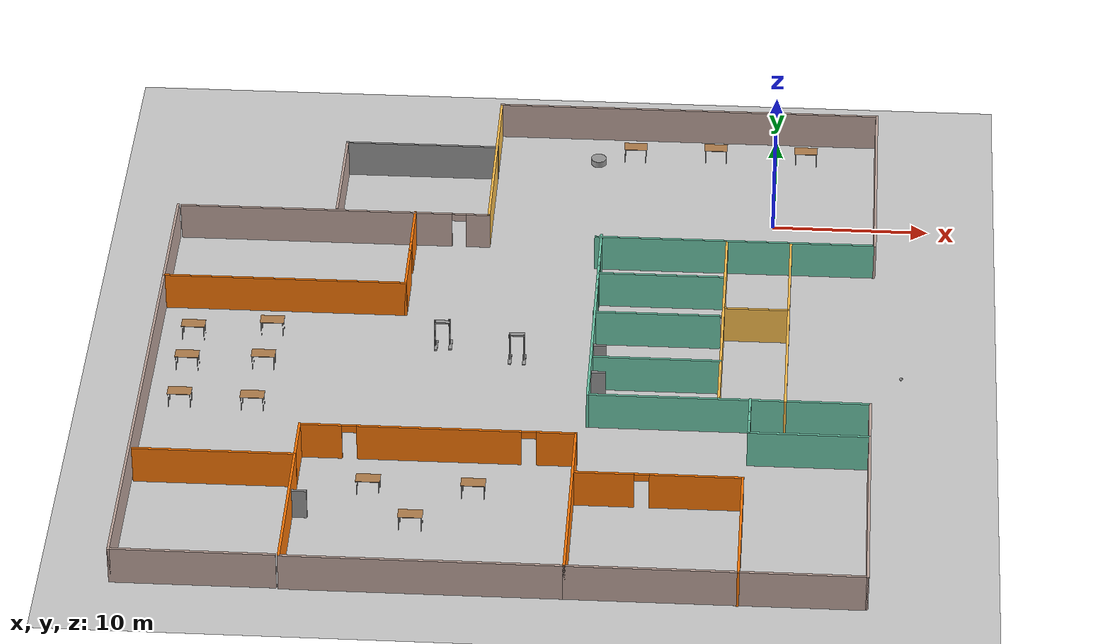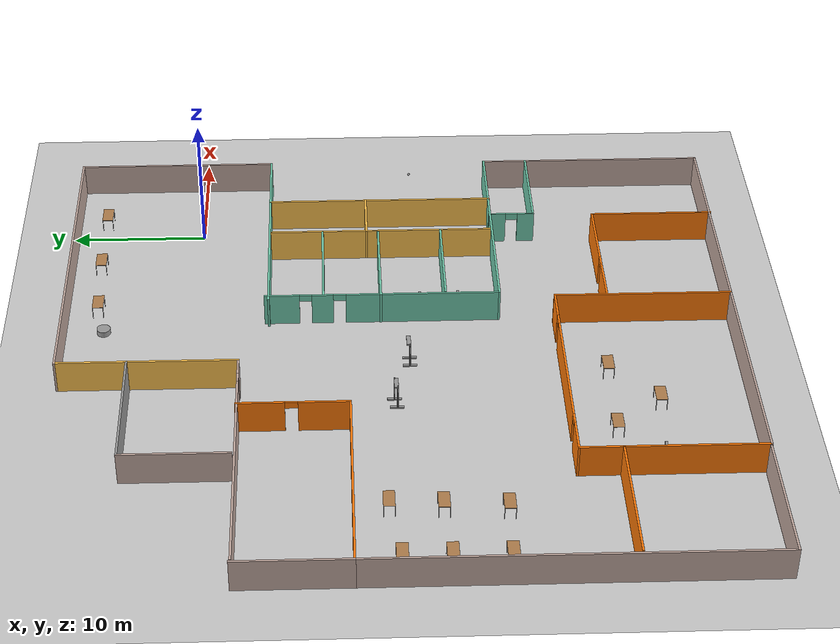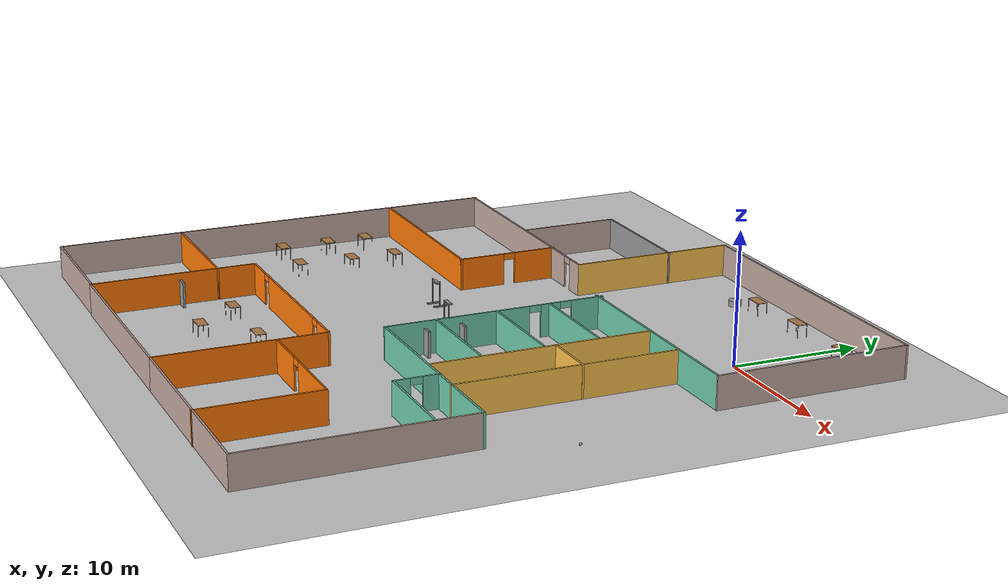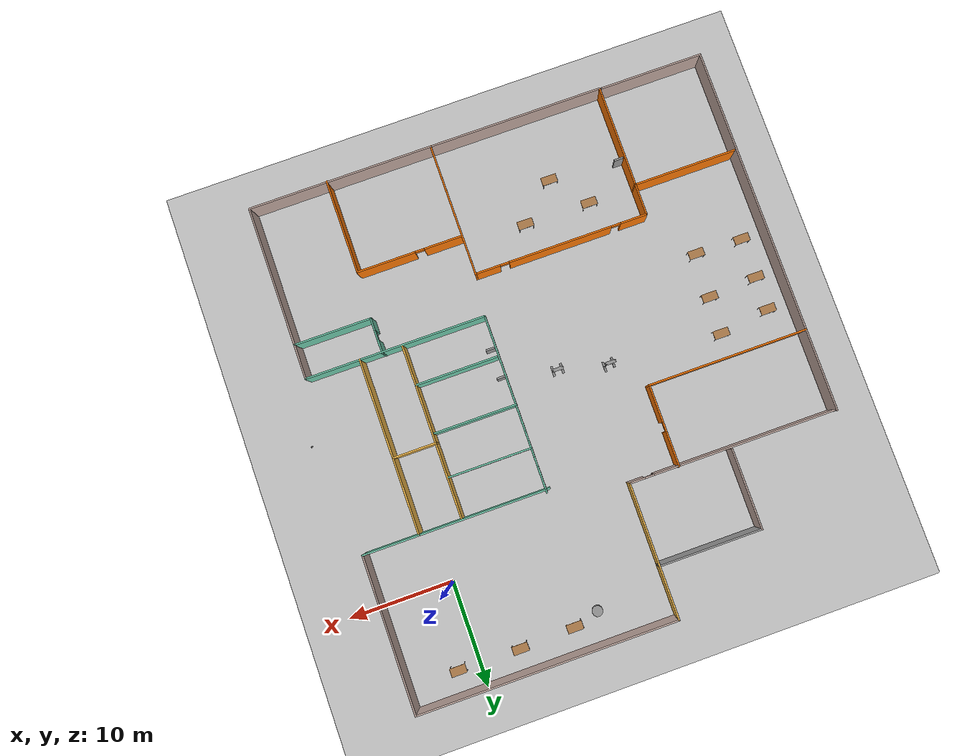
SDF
<sdf version="1.6">
 <world name="default">
  <plugin name="hello" filename="libhello.so"/>
  <light name="sun" type="directional">
   <pose>0 0 10 0 -0 0</pose>
   <diffuse>0.8 0.8 0.8 1</diffuse>
   <specular>0.2 0.2 0.2 1</specular>
   <attenuation>
    <range>1000</range>
    <constant>0.9</constant>
    <linear>0.01</linear>
    <quadratic>0.001</quadratic>
   </attenuation>
   <direction>-0.5 0.1 -0.9</direction>
  </light>
  <model name="ground_plane">
   <static>1</static>
   <link name="link">
    <collision name="collision">
     <geometry><plane><normal>0 0 1</normal><size>100 100</size></plane></geometry>
     <surface>
      <contact><collide_bitmask>65535</collide_bitmask></contact>
      <friction><ode><mu>100</mu><mu2>50</mu2></ode></friction>
     </surface>
    </collision>
    <visual name="visual">
     <cast_shadows>0</cast_shadows>
     <geometry><plane><normal>0 0 1</normal><size>100 100</size></plane></geometry>
     <material>
      <script><uri>file://media/materials/scripts/gazebo.material</uri><name>Gazebo/Grey</name></script>
     </material>
    </visual>
   </link>
  </model>
  <gravity>0 0 -9.8</gravity>
  <magnetic_field>6e-06 2.3e-05 -4.2e-05</magnetic_field>
  <atmosphere type="adiabatic"/>
  <physics name="default_physics" default="0" type="ode">
   <max_step_size>0.001</max_step_size>
   <real_time_factor>1</real_time_factor>
   <real_time_update_rate>1000</real_time_update_rate>
  </physics>
  <scene><ambient>0.4 0.4 0.4 1</ambient><background>0.7 0.7 0.7 1</background><shadows>1</shadows></scene>
  <spherical_coordinates>
   <surface_model>EARTH_WGS84</surface_model>
   <latitude_deg>0</latitude_deg>
   <longitude_deg>0</longitude_deg>
   <elevation>0</elevation>
   <heading_deg>0</heading_deg>
  </spherical_coordinates>
  <model name="newest">
   <pose>-15.9063 -14.6131 0 0 -0 0</pose>
   <link name="Door_4">
    <collision name="Door_4_Collision">
     <geometry><box><size>0.9 0.17 2</size></box></geometry>
     <pose>0 0 1 0 -0 0</pose>
    </collision>
    <visual name="Door_4_Visual">
     <pose>0 0 1 0 -0 0</pose>
     <geometry><box><size>0.9 0.17 2</size></box></geometry>
     <material>
      <script><uri>file://media/materials/scripts/gazebo.material</uri><name>Gazebo/Grey</name></script>
     </material>
    </visual>
    <pose>5.40167 -1.58767 0 0 -0 0</pose>
   </link>
   <link name="Door_5">
    <collision name="Door_5_Collision">
     <geometry><box><size>0.9 0.17 2</size></box></geometry>
     <pose>0 0 1 0 -0 0</pose>
    </collision>
    <visual name="Door_5_Visual">
     <pose>0 0 1 0 -0 0</pose>
     <geometry><box><size>0.9 0.17 2</size></box></geometry>
     <material>
      <script><uri>file://media/materials/scripts/gazebo.material</uri><name>Gazebo/Grey</name></script>
     </material>
    </visual>
    <pose>5.49524 -4.39496 0 0 -0 0</pose>
   </link>
   <link name="Door_7">
    <collision name="Door_7_Collision">
     <geometry><box><size>0.9 0.17 2</size></box></geometry>
     <pose>0 0 1 0 -0 0</pose>
    </collision>
    <visual name="Door_7_Visual">
     <pose>0 0 1 0 -0 0</pose>
     <geometry><box><size>0.9 0.17 2</size></box></geometry>
     <material>
      <script><uri>file://media/materials/scripts/gazebo.material</uri><name>Gazebo/Grey</name></script>
     </material>
    </visual>
    <pose>-11.8428 -17.3645 0 0 -0 0</pose>
   </link>
   <link name="Wall_1">
    <collision name="Wall_1_Collision">
     <geometry><box><size>25 0.15 2.5</size></box></geometry>
     <pose>0 0 1.25 0 -0 0</pose>
    </collision>
    <visual name="Wall_1_Visual">
     <pose>0 0 1.25 0 -0 0</pose>
     <geometry><box><size>25 0.15 2.5</size></box></geometry>
     <material>
      <script><uri>file://media/materials/scripts/gazebo.material</uri><name>Gazebo/Grey</name></script>
      <ambient>0.760784 0.662745 0.627451 1</ambient>
     </material>
     <meta><layer>0</layer></meta>
    </visual>
    <pose>10.0497 24.3037 0 0 -0 0</pose>
   </link>
   <link name="Wall_11">
    <collision name="Wall_11_Collision">
     <geometry><box><size>10 0.15 2.5</size></box></geometry>
     <pose>0 0 1.25 0 -0 0</pose>
    </collision>
    <visual name="Wall_11_Visual">
     <pose>0 0 1.25 0 -0 0</pose>
     <geometry><box><size>10 0.15 2.5</size></box></geometry>
     <material>
      <script><uri>file://media/materials/scripts/gazebo.material</uri><name>Gazebo/Grey</name></script>
      <ambient>1 1 1 1</ambient>
     </material>
     <meta><layer>0</layer></meta>
    </visual>
    <pose>-7.27616 19.2697 0 0 -0 3.14159</pose>
   </link>
   <link name="Wall_13">
    <collision name="Wall_13_Collision">
     <geometry><box><size>7.75 0.15 2.5</size></box></geometry>
     <pose>0 0 1.25 0 -0 0</pose>
    </collision>
    <visual name="Wall_13_Visual">
     <pose>0 0 1.25 0 -0 0</pose>
     <geometry><box><size>7.75 0.15 2.5</size></box></geometry>
     <material>
      <script><uri>file://media/materials/scripts/gazebo.material</uri><name>Gazebo/Grey</name></script>
      <ambient>0.760784 0.662745 0.627451 1</ambient>
     </material>
     <meta><layer>0</layer></meta>
    </visual>
    <pose>-12.2012 15.4697 0 0 0 -1.5708</pose>
   </link>
   <link name="Wall_15">
    <collision name="Wall_15_Collision">
     <geometry><box><size>8 0.15 2.5</size></box></geometry>
     <pose>0 0 1.25 0 -0 0</pose>
    </collision>
    <visual name="Wall_15_Visual">
     <pose>0 0 1.25 0 -0 0</pose>
     <geometry><box><size>8 0.15 2.5</size></box></geometry>
     <material>
      <script><uri>file://media/materials/scripts/gazebo.material</uri><name>Gazebo/Grey</name></script>
      <ambient>0.760784 0.662745 0.627451 1</ambient>
     </material>
     <meta><layer>0</layer></meta>
    </visual>
    <pose>-22.4747 7.59655 0 0 0 -1.5708</pose>
   </link>
   <link name="Wall_17">
    <collision name="Wall_17_Collision">
     <geometry><box><size>15.5 0.15 2.5</size></box></geometry>
     <pose>0 0 1.25 0 -0 0</pose>
    </collision>
    <visual name="Wall_17_Visual">
     <pose>0 0 1.25 0 -0 0</pose>
     <geometry><box><size>15.5 0.15 2.5</size></box></geometry>
     <material>
      <script><uri>file://media/materials/scripts/gazebo.material</uri><name>Gazebo/Grey</name></script>
      <ambient>0.996078 0.47451 0.0196078 1</ambient>
     </material>
     <meta><layer>0</layer></meta>
    </visual>
    <pose>-14.7997 3.67155 0 0 -0 0</pose>
   </link>
   <link name="Wall_18">
    <pose>-7.12473 7.59655 0 0 -0 1.5708</pose>
    <visual name="Wall_18_Visual_0">
     <pose>-2.16447 0 1.25 0 -0 0</pose>
     <geometry><box><size>3.67106 0.15 2.5</size></box></geometry>
     <material>
      <script><uri>file://media/materials/scripts/gazebo.material</uri><name>Gazebo/Grey</name></script>
      <ambient>0.996078 0.47451 0.0196078 1</ambient>
     </material>
     <meta><layer>0</layer></meta>
    </visual>
    <collision name="Wall_18_Collision_0">
     <geometry><box><size>3.67106 0.15 2.5</size></box></geometry>
     <pose>-2.16447 0 1.25 0 -0 0</pose>
    </collision>
    <visual name="Wall_18_Visual_1">
     <pose>2.28553 0 1.25 0 -0 0</pose>
     <geometry><box><size>3.42894 0.15 2.5</size></box></geometry>
     <material>
      <script><uri>file://media/materials/scripts/gazebo.material</uri><name>Gazebo/Grey</name></script>
      <ambient>0.996078 0.47451 0.0196078 1</ambient>
     </material>
     <meta><layer>0</layer></meta>
    </visual>
    <collision name="Wall_18_Collision_1">
     <geometry><box><size>3.42894 0.15 2.5</size></box></geometry>
     <pose>2.28553 0 1.25 0 -0 0</pose>
    </collision>
    <visual name="Wall_18_Visual_2">
     <pose>0.121058 0 2.25 0 -0 0</pose>
     <geometry><box><size>0.9 0.15 0.5</size></box></geometry>
     <material>
      <script><uri>file://media/materials/scripts/gazebo.material</uri><name>Gazebo/Grey</name></script>
      <ambient>0.996078 0.47451 0.0196078 1</ambient>
     </material>
     <meta><layer>0</layer></meta>
    </visual>
    <collision name="Wall_18_Collision_2">
     <geometry><box><size>0.9 0.15 0.5</size></box></geometry>
     <pose>0.121058 0 2.25 0 -0 0</pose>
    </collision>
   </link>
   <link name="Wall_20">
    <collision name="Wall_20_Collision">
     <geometry><box><size>28 0.15 2.5</size></box></geometry>
     <pose>0 0 1.25 0 -0 0</pose>
    </collision>
    <visual name="Wall_20_Visual">
     <pose>0 0 1.25 0 -0 0</pose>
     <geometry><box><size>28 0.15 2.5</size></box></geometry>
     <material>
      <script><uri>file://media/materials/scripts/gazebo.material</uri><name>Gazebo/Grey</name></script>
      <ambient>0.760784 0.662745 0.627451 1</ambient>
     </material>
     <meta><layer>0</layer></meta>
    </visual>
    <pose>-22.4747 -10.2535 0 0 0 -1.5708</pose>
   </link>
   <link name="Wall_22">
    <collision name="Wall_22_Collision">
     <geometry><box><size>10 0.15 2.5</size></box></geometry>
     <pose>0 0 1.25 0 -0 0</pose>
    </collision>
    <visual name="Wall_22_Visual">
     <pose>0 0 1.25 0 -0 0</pose>
     <geometry><box><size>10 0.15 2.5</size></box></geometry>
     <material>
      <script><uri>file://media/materials/scripts/gazebo.material</uri><name>Gazebo/Grey</name></script>
      <ambient>0.760784 0.662745 0.627451 1</ambient>
     </material>
     <meta><layer>0</layer></meta>
    </visual>
    <pose>-17.5497 -24.1785 0 0 -0 0</pose>
   </link>
   <link name="Wall_24">
    <collision name="Wall_24_Collision">
     <geometry><box><size>10 0.15 2.5</size></box></geometry>
     <pose>0 0 1.25 0 -0 0</pose>
    </collision>
    <visual name="Wall_24_Visual">
     <pose>0 0 1.25 0 -0 0</pose>
     <geometry><box><size>10 0.15 2.5</size></box></geometry>
     <material>
      <script><uri>file://media/materials/scripts/gazebo.material</uri><name>Gazebo/Grey</name></script>
      <ambient>0.996078 0.47451 0.0196078 1</ambient>
     </material>
     <meta><layer>0</layer></meta>
    </visual>
    <pose>-12.3763 -19.3183 0 0 -0 1.5708</pose>
   </link>
   <link name="Wall_26">
    <collision name="Wall_26_Collision">
     <geometry><box><size>10 0.15 2.5</size></box></geometry>
     <pose>0 0 1.25 0 -0 0</pose>
    </collision>
    <visual name="Wall_26_Visual">
     <pose>0 0 1.25 0 -0 0</pose>
     <geometry><box><size>10 0.15 2.5</size></box></geometry>
     <material>
      <script><uri>file://media/materials/scripts/gazebo.material</uri><name>Gazebo/Grey</name></script>
      <ambient>0.996078 0.47451 0.0196078 1</ambient>
     </material>
     <meta><layer>0</layer></meta>
    </visual>
    <pose>-17.3013 -14.3933 0 0 -0 3.14159</pose>
   </link>
   <link name="Wall_28">
    <collision name="Wall_28_Collision">
     <geometry><box><size>17 0.15 2.5</size></box></geometry>
     <pose>0 0 1.25 0 -0 0</pose>
    </collision>
    <visual name="Wall_28_Visual">
     <pose>0 0 1.25 0 -0 0</pose>
     <geometry><box><size>17 0.15 2.5</size></box></geometry>
     <material>
      <script><uri>file://media/materials/scripts/gazebo.material</uri><name>Gazebo/Grey</name></script>
      <ambient>0.760784 0.662745 0.627451 1</ambient>
     </material>
     <meta><layer>0</layer></meta>
    </visual>
    <pose>-3.95132 -24.2434 0 0 -0 0</pose>
   </link>
   <link name="Wall_3">
    <collision name="Wall_3_Collision">
     <geometry><box><size>15 0.15 2.5</size></box></geometry>
     <pose>0 0 1.25 0 -0 0</pose>
    </collision>
    <visual name="Wall_3_Visual">
     <pose>0 0 1.25 0 -0 0</pose>
     <geometry><box><size>15 0.15 2.5</size></box></geometry>
     <material>
      <script><uri>file://media/materials/scripts/gazebo.material</uri><name>Gazebo/Grey</name></script>
      <ambient>0.760784 0.662745 0.627451 1</ambient>
     </material>
     <meta><layer>0</layer></meta>
    </visual>
    <pose>22.4745 16.8789 0 0 0 -1.57082</pose>
   </link>
   <link name="Wall_30">
    <collision name="Wall_30_Collision">
     <geometry><box><size>13 0.15 2.5</size></box></geometry>
     <pose>0 0 1.25 0 -0 0</pose>
    </collision>
    <visual name="Wall_30_Visual">
     <pose>0 0 1.25 0 -0 0</pose>
     <geometry><box><size>13 0.15 2.5</size></box></geometry>
     <material>
      <script><uri>file://media/materials/scripts/gazebo.material</uri><name>Gazebo/Grey</name></script>
      <ambient>0.996078 0.47451 0.0196078 1</ambient>
     </material>
     <meta><layer>0</layer></meta>
    </visual>
    <pose>4.47368 -17.8183 0 0 -0 1.5708</pose>
   </link>
   <link name="Wall_31">
    <pose>-3.95132 -11.3933 0 0 -0 3.14159</pose>
    <visual name="Wall_31_Visual_0">
     <pose>-7.25826 0 1.25 0 -0 0</pose>
     <geometry><box><size>2.48348 0.15 2.5</size></box></geometry>
     <material>
      <script><uri>file://media/materials/scripts/gazebo.material</uri><name>Gazebo/Grey</name></script>
      <ambient>0.996078 0.47451 0.0196078 1</ambient>
     </material>
     <meta><layer>0</layer></meta>
    </visual>
    <collision name="Wall_31_Collision_0">
     <geometry><box><size>2.48348 0.15 2.5</size></box></geometry>
     <pose>-7.25826 0 1.25 0 -0 0</pose>
    </collision>
    <visual name="Wall_31_Visual_1">
     <pose>-0.083725 0 1.25 0 -0 0</pose>
     <geometry><box><size>10.0656 0.15 2.5</size></box></geometry>
     <material>
      <script><uri>file://media/materials/scripts/gazebo.material</uri><name>Gazebo/Grey</name></script>
      <ambient>0.996078 0.47451 0.0196078 1</ambient>
     </material>
     <meta><layer>0</layer></meta>
    </visual>
    <collision name="Wall_31_Collision_1">
     <geometry><box><size>10.0656 0.15 2.5</size></box></geometry>
     <pose>-0.083725 0 1.25 0 -0 0</pose>
    </collision>
    <visual name="Wall_31_Visual_2">
     <pose>7.17453 0 1.25 0 -0 0</pose>
     <geometry><box><size>2.65094 0.15 2.5</size></box></geometry>
     <material>
      <script><uri>file://media/materials/scripts/gazebo.material</uri><name>Gazebo/Grey</name></script>
      <ambient>0.996078 0.47451 0.0196078 1</ambient>
     </material>
     <meta><layer>0</layer></meta>
    </visual>
    <collision name="Wall_31_Collision_2">
     <geometry><box><size>2.65094 0.15 2.5</size></box></geometry>
     <pose>7.17453 0 1.25 0 -0 0</pose>
    </collision>
    <visual name="Wall_31_Visual_3">
     <pose>-5.56652 0 2.25 0 -0 0</pose>
     <geometry><box><size>0.9 0.15 0.5</size></box></geometry>
     <material>
      <script><uri>file://media/materials/scripts/gazebo.material</uri><name>Gazebo/Grey</name></script>
      <ambient>0.996078 0.47451 0.0196078 1</ambient>
     </material>
     <meta><layer>0</layer></meta>
    </visual>
    <collision name="Wall_31_Collision_3">
     <geometry><box><size>0.9 0.15 0.5</size></box></geometry>
     <pose>-5.56652 0 2.25 0 -0 0</pose>
    </collision>
    <visual name="Wall_31_Visual_4">
     <pose>5.39907 0 2.25 0 -0 0</pose>
     <geometry><box><size>0.9 0.15 0.5</size></box></geometry>
     <material>
      <script><uri>file://media/materials/scripts/gazebo.material</uri><name>Gazebo/Grey</name></script>
      <ambient>0.996078 0.47451 0.0196078 1</ambient>
     </material>
     <meta><layer>0</layer></meta>
    </visual>
    <collision name="Wall_31_Collision_4">
     <geometry><box><size>0.9 0.15 0.5</size></box></geometry>
     <pose>5.39907 0 2.25 0 -0 0</pose>
    </collision>
   </link>
   <link name="Wall_32">
    <collision name="Wall_32_Collision">
     <geometry><box><size>3.15 0.15 2.5</size></box></geometry>
     <pose>0 0 1.25 0 -0 0</pose>
    </collision>
    <visual name="Wall_32_Visual">
     <pose>0 0 1.25 0 -0 0</pose>
     <geometry><box><size>3.15 0.15 2.5</size></box></geometry>
     <material>
      <script><uri>file://media/materials/scripts/gazebo.material</uri><name>Gazebo/Grey</name></script>
      <ambient>0.996078 0.47451 0.0196078 1</ambient>
     </material>
     <meta><layer>0</layer></meta>
    </visual>
    <pose>-12.3763 -12.8933 0 0 0 -1.5708</pose>
   </link>
   <link name="Wall_34">
    <collision name="Wall_34_Collision">
     <geometry><box><size>18 0.15 2.5</size></box></geometry>
     <pose>0 0 1.25 0 -0 0</pose>
    </collision>
    <visual name="Wall_34_Visual">
     <pose>0 0 1.25 0 -0 0</pose>
     <geometry><box><size>18 0.15 2.5</size></box></geometry>
     <material>
      <script><uri>file://media/materials/scripts/gazebo.material</uri><name>Gazebo/Grey</name></script>
      <ambient>0.760784 0.662745 0.627451 1</ambient>
     </material>
     <meta><layer>0</layer></meta>
    </visual>
    <pose>13.3987 -24.2434 0 0 -0 0</pose>
   </link>
   <link name="Wall_35">
    <collision name="Wall_35_Collision">
     <geometry><box><size>17 0.15 2.5</size></box></geometry>
     <pose>0 0 1.25 0 -0 0</pose>
    </collision>
    <visual name="Wall_35_Visual">
     <pose>0 0 1.25 0 -0 0</pose>
     <geometry><box><size>17 0.15 2.5</size></box></geometry>
     <material>
      <script><uri>file://media/materials/scripts/gazebo.material</uri><name>Gazebo/Grey</name></script>
      <ambient>0.760784 0.662745 0.627451 1</ambient>
     </material>
     <meta><layer>0</layer></meta>
    </visual>
    <pose>22.3237 -15.8184 0 0 -0 1.5708</pose>
   </link>
   <link name="Wall_36">
    <collision name="Wall_36_Collision">
     <geometry><box><size>17.5 0.15 2.5</size></box></geometry>
     <pose>0 0 1.25 0 -0 0</pose>
    </collision>
    <visual name="Wall_36_Visual">
     <pose>0 0 1.25 0 -0 0</pose>
     <geometry><box><size>17.5 0.15 2.5</size></box></geometry>
     <material>
      <script><uri>file://media/materials/scripts/gazebo.material</uri><name>Gazebo/Grey</name></script>
      <ambient>0.435294 0.796078 0.67451 1</ambient>
     </material>
     <meta><layer>0</layer></meta>
    </visual>
    <pose>13.6487 -7.39335 0 0 -0 3.14159</pose>
   </link>
   <link name="Wall_37">
    <pose>4.97368 1.15665 0 0 -0 1.5708</pose>
    <visual name="Wall_37_Visual_0">
     <pose>-2.97883 0 1.25 0 -0 0</pose>
     <geometry><box><size>11.2924 0.15 2.5</size></box></geometry>
     <material>
      <script><uri>file://media/materials/scripts/gazebo.material</uri><name>Gazebo/Grey</name></script>
      <ambient>0.435294 0.796078 0.67451 1</ambient>
     </material>
     <meta><layer>0</layer></meta>
    </visual>
    <collision name="Wall_37_Collision_0">
     <geometry><box><size>11.2924 0.15 2.5</size></box></geometry>
     <pose>-2.97883 0 1.25 0 -0 0</pose>
    </collision>
    <visual name="Wall_37_Visual_1">
     <pose>4.35489 0 1.25 0 -0 0</pose>
     <geometry><box><size>1.57509 0.15 2.5</size></box></geometry>
     <material>
      <script><uri>file://media/materials/scripts/gazebo.material</uri><name>Gazebo/Grey</name></script>
      <ambient>0.435294 0.796078 0.67451 1</ambient>
     </material>
     <meta><layer>0</layer></meta>
    </visual>
    <collision name="Wall_37_Collision_1">
     <geometry><box><size>1.57509 0.15 2.5</size></box></geometry>
     <pose>4.35489 0 1.25 0 -0 0</pose>
    </collision>
    <visual name="Wall_37_Visual_2">
     <pose>7.33372 0 1.25 0 -0 0</pose>
     <geometry><box><size>2.58256 0.15 2.5</size></box></geometry>
     <material>
      <script><uri>file://media/materials/scripts/gazebo.material</uri><name>Gazebo/Grey</name></script>
      <ambient>0.435294 0.796078 0.67451 1</ambient>
     </material>
     <meta><layer>0</layer></meta>
    </visual>
    <collision name="Wall_37_Collision_2">
     <geometry><box><size>2.58256 0.15 2.5</size></box></geometry>
     <pose>7.33372 0 1.25 0 -0 0</pose>
    </collision>
    <visual name="Wall_37_Visual_3">
     <pose>3.11735 0 2.25 0 -0 0</pose>
     <geometry><box><size>0.9 0.15 0.5</size></box></geometry>
     <material>
      <script><uri>file://media/materials/scripts/gazebo.material</uri><name>Gazebo/Grey</name></script>
      <ambient>0.435294 0.796078 0.67451 1</ambient>
     </material>
     <meta><layer>0</layer></meta>
    </visual>
    <collision name="Wall_37_Collision_3">
     <geometry><box><size>0.9 0.15 0.5</size></box></geometry>
     <pose>3.11735 0 2.25 0 -0 0</pose>
    </collision>
    <visual name="Wall_37_Visual_4">
     <pose>5.59244 0 2.25 0 -0 0</pose>
     <geometry><box><size>0.9 0.15 0.5</size></box></geometry>
     <material>
      <script><uri>file://media/materials/scripts/gazebo.material</uri><name>Gazebo/Grey</name></script>
      <ambient>0.435294 0.796078 0.67451 1</ambient>
     </material>
     <meta><layer>0</layer></meta>
    </visual>
    <collision name="Wall_37_Collision_4">
     <geometry><box><size>0.9 0.15 0.5</size></box></geometry>
     <pose>5.59244 0 2.25 0 -0 0</pose>
    </collision>
   </link>
   <link name="Wall_39">
    <pose>9.67648 -15.2039 0 0 -0 0</pose>
    <visual name="Wall_39_Visual_0">
     <pose>-3.29934 0 1.25 0 -0 0</pose>
     <geometry><box><size>3.65133 0.15 2.5</size></box></geometry>
     <material>
      <script><uri>file://media/materials/scripts/gazebo.material</uri><name>Gazebo/Grey</name></script>
      <ambient>0.996078 0.47451 0.0196078 1</ambient>
     </material>
     <meta><layer>0</layer></meta>
    </visual>
    <collision name="Wall_39_Collision_0">
     <geometry><box><size>3.65133 0.15 2.5</size></box></geometry>
     <pose>-3.29934 0 1.25 0 -0 0</pose>
    </collision>
    <visual name="Wall_39_Visual_1">
     <pose>2.27567 0 1.25 0 -0 0</pose>
     <geometry><box><size>5.69867 0.15 2.5</size></box></geometry>
     <material>
      <script><uri>file://media/materials/scripts/gazebo.material</uri><name>Gazebo/Grey</name></script>
      <ambient>0.996078 0.47451 0.0196078 1</ambient>
     </material>
     <meta><layer>0</layer></meta>
    </visual>
    <collision name="Wall_39_Collision_1">
     <geometry><box><size>5.69867 0.15 2.5</size></box></geometry>
     <pose>2.27567 0 1.25 0 -0 0</pose>
    </collision>
    <visual name="Wall_39_Visual_2">
     <pose>-1.02367 0 2.25 0 -0 0</pose>
     <geometry><box><size>0.9 0.15 0.5</size></box></geometry>
     <material>
      <script><uri>file://media/materials/scripts/gazebo.material</uri><name>Gazebo/Grey</name></script>
      <ambient>0.996078 0.47451 0.0196078 1</ambient>
     </material>
     <meta><layer>0</layer></meta>
    </visual>
    <collision name="Wall_39_Collision_2">
     <geometry><box><size>0.9 0.15 0.5</size></box></geometry>
     <pose>-1.02367 0 2.25 0 -0 0</pose>
    </collision>
   </link>
   <link name="Wall_40">
    <collision name="Wall_40_Collision">
     <geometry><box><size>9.25 0.15 2.5</size></box></geometry>
     <pose>0 0 1.25 0 -0 0</pose>
    </collision>
    <visual name="Wall_40_Visual">
     <pose>0 0 1.25 0 -0 0</pose>
     <geometry><box><size>9.25 0.15 2.5</size></box></geometry>
     <material>
      <script><uri>file://media/materials/scripts/gazebo.material</uri><name>Gazebo/Grey</name></script>
      <ambient>0.996078 0.47451 0.0196078 1</ambient>
     </material>
     <meta><layer>0</layer></meta>
    </visual>
    <pose>14.7265 -19.7539 0 0 0 -1.5708</pose>
   </link>
   <link name="Wall_42">
    <collision name="Wall_42_Collision">
     <geometry><box><size>17 0.15 2.5</size></box></geometry>
     <pose>0 0 1.25 0 -0 0</pose>
    </collision>
    <visual name="Wall_42_Visual">
     <pose>0 0 1.25 0 -0 0</pose>
     <geometry><box><size>17 0.15 2.5</size></box></geometry>
     <material>
      <script><uri>file://media/materials/scripts/gazebo.material</uri><name>Gazebo/Grey</name></script>
      <ambient>1 0.764706 0.305882 1</ambient>
     </material>
     <meta><layer>0</layer></meta>
    </visual>
    <pose>17.1095 1.01441 0 0 0 -1.5708</pose>
   </link>
   <link name="Wall_44">
    <collision name="Wall_44_Collision">
     <geometry><box><size>16.75 0.15 2.5</size></box></geometry>
     <pose>0 0 1.25 0 -0 0</pose>
    </collision>
    <visual name="Wall_44_Visual">
     <pose>0 0 1.25 0 -0 0</pose>
     <geometry><box><size>16.75 0.15 2.5</size></box></geometry>
     <material>
      <script><uri>file://media/materials/scripts/gazebo.material</uri><name>Gazebo/Grey</name></script>
      <ambient>1 0.764706 0.305882 1</ambient>
     </material>
     <meta><layer>0</layer></meta>
    </visual>
    <pose>13.0203 1.0318 0 0 0 -1.5708</pose>
   </link>
   <link name="Wall_46">
    <collision name="Wall_46_Collision">
     <geometry><box><size>8 0.15 2.5</size></box></geometry>
     <pose>0 0 1.25 0 -0 0</pose>
    </collision>
    <visual name="Wall_46_Visual">
     <pose>0 0 1.25 0 -0 0</pose>
     <geometry><box><size>8 0.15 2.5</size></box></geometry>
     <material>
      <script><uri>file://media/materials/scripts/gazebo.material</uri><name>Gazebo/Grey</name></script>
      <ambient>0.435294 0.796078 0.67451 1</ambient>
     </material>
     <meta><layer>0</layer></meta>
    </visual>
    <pose>8.98193 5.45774 0 0 -0 0</pose>
   </link>
   <link name="Wall_48">
    <collision name="Wall_48_Collision">
     <geometry><box><size>8 0.15 2.5</size></box></geometry>
     <pose>0 0 1.25 0 -0 0</pose>
    </collision>
    <visual name="Wall_48_Visual">
     <pose>0 0 1.25 0 -0 0</pose>
     <geometry><box><size>8 0.15 2.5</size></box></geometry>
     <material>
      <script><uri>file://media/materials/scripts/gazebo.material</uri><name>Gazebo/Grey</name></script>
      <ambient>0.435294 0.796078 0.67451 1</ambient>
     </material>
     <meta><layer>0</layer></meta>
    </visual>
    <pose>8.87432 1.26085 0 0 -0 0</pose>
   </link>
   <link name="Wall_5">
    <collision name="Wall_5_Collision">
     <geometry><box><size>18 0.15 2.5</size></box></geometry>
     <pose>0 0 1.25 0 -0 0</pose>
    </collision>
    <visual name="Wall_5_Visual">
     <pose>0 0 1.25 0 -0 0</pose>
     <geometry><box><size>18 0.15 2.5</size></box></geometry>
     <material>
      <script><uri>file://media/materials/scripts/gazebo.material</uri><name>Gazebo/Grey</name></script>
      <ambient>0.435294 0.796078 0.67451 1</ambient>
     </material>
     <meta><layer>0</layer></meta>
    </visual>
    <pose>13.5493 9.45408 0 0 -0 3.14159</pose>
   </link>
   <link name="Wall_50">
    <collision name="Wall_50_Collision">
     <geometry><box><size>8 0.15 2.5</size></box></geometry>
     <pose>0 0 1.25 0 -0 0</pose>
    </collision>
    <visual name="Wall_50_Visual">
     <pose>0 0 1.25 0 -0 0</pose>
     <geometry><box><size>8 0.15 2.5</size></box></geometry>
     <material>
      <script><uri>file://media/materials/scripts/gazebo.material</uri><name>Gazebo/Grey</name></script>
      <ambient>0.435294 0.796078 0.67451 1</ambient>
     </material>
     <meta><layer>0</layer></meta>
    </visual>
    <pose>9.08954 -3.47411 0 0 -0 0</pose>
   </link>
   <link name="Wall_52">
    <collision name="Wall_52_Collision">
     <geometry><box><size>4.25 0.15 2.5</size></box></geometry>
     <pose>0 0 1.25 0 -0 0</pose>
    </collision>
    <visual name="Wall_52_Visual">
     <pose>0 0 1.25 0 -0 0</pose>
     <geometry><box><size>4.25 0.15 2.5</size></box></geometry>
     <material>
      <script><uri>file://media/materials/scripts/gazebo.material</uri><name>Gazebo/Grey</name></script>
      <ambient>1 0.764706 0.305882 1</ambient>
     </material>
     <meta><layer>0</layer></meta>
    </visual>
    <pose>15.0703 2.12175 0 0 -0 0</pose>
   </link>
   <link name="Wall_54">
    <pose>14.9573 -9.02317 0 0 0 -1.5708</pose>
    <visual name="Wall_54_Visual_0">
     <pose>-1.09496 0 1.25 0 -0 0</pose>
     <geometry><box><size>1.31008 0.15 2.5</size></box></geometry>
     <material>
      <script><uri>file://media/materials/scripts/gazebo.material</uri><name>Gazebo/Grey</name></script>
      <ambient>0.435294 0.796078 0.67451 1</ambient>
     </material>
     <meta><layer>0</layer></meta>
    </visual>
    <collision name="Wall_54_Collision_0">
     <geometry><box><size>1.31008 0.15 2.5</size></box></geometry>
     <pose>-1.09496 0 1.25 0 -0 0</pose>
    </collision>
    <visual name="Wall_54_Visual_1">
     <pose>1.10504 0 1.25 0 -0 0</pose>
     <geometry><box><size>1.28992 0.15 2.5</size></box></geometry>
     <material>
      <script><uri>file://media/materials/scripts/gazebo.material</uri><name>Gazebo/Grey</name></script>
      <ambient>0.435294 0.796078 0.67451 1</ambient>
     </material>
     <meta><layer>0</layer></meta>
    </visual>
    <collision name="Wall_54_Collision_1">
     <geometry><box><size>1.28992 0.15 2.5</size></box></geometry>
     <pose>1.10504 0 1.25 0 -0 0</pose>
    </collision>
    <visual name="Wall_54_Visual_2">
     <pose>0.010077 0 2.25 0 -0 0</pose>
     <geometry><box><size>0.9 0.15 0.5</size></box></geometry>
     <material>
      <script><uri>file://media/materials/scripts/gazebo.material</uri><name>Gazebo/Grey</name></script>
      <ambient>0.435294 0.796078 0.67451 1</ambient>
     </material>
     <meta><layer>0</layer></meta>
    </visual>
    <collision name="Wall_54_Collision_2">
     <geometry><box><size>0.9 0.15 0.5</size></box></geometry>
     <pose>0.010077 0 2.25 0 -0 0</pose>
    </collision>
   </link>
   <link name="Wall_55">
    <collision name="Wall_55_Collision">
     <geometry><box><size>7.5 0.15 2.5</size></box></geometry>
     <pose>0 0 1.25 0 -0 0</pose>
    </collision>
    <visual name="Wall_55_Visual">
     <pose>0 0 1.25 0 -0 0</pose>
     <geometry><box><size>7.5 0.15 2.5</size></box></geometry>
     <material>
      <script><uri>file://media/materials/scripts/gazebo.material</uri><name>Gazebo/Grey</name></script>
      <ambient>0.435294 0.796078 0.67451 1</ambient>
     </material>
     <meta><layer>0</layer></meta>
    </visual>
    <pose>18.6323 -10.6982 0 0 -0 0</pose>
   </link>
   <link name="Wall_7">
    <collision name="Wall_7_Collision">
     <geometry><box><size>13 0.15 2.5</size></box></geometry>
     <pose>0 0 1.25 0 -0 0</pose>
    </collision>
    <visual name="Wall_7_Visual">
     <pose>0 0 1.25 0 -0 0</pose>
     <geometry><box><size>13 0.15 2.5</size></box></geometry>
     <material>
      <script><uri>file://media/materials/scripts/gazebo.material</uri><name>Gazebo/Grey</name></script>
      <ambient>1 0.764706 0.305882 1</ambient>
     </material>
     <meta><layer>0</layer></meta>
    </visual>
    <pose>-2.37527 17.8787 0 0 0 -1.5708</pose>
   </link>
   <link name="Wall_9">
    <pose>-12.3003 11.4537 0 0 -0 3.14159</pose>
    <visual name="Wall_9_Visual_0">
     <pose>-9.22245 0 1.25 0 -0 0</pose>
     <geometry><box><size>1.55509 0.15 2.5</size></box></geometry>
     <material>
      <script><uri>file://media/materials/scripts/gazebo.material</uri><name>Gazebo/Grey</name></script>
      <ambient>0.760784 0.662745 0.627451 1</ambient>
     </material>
     <meta><layer>0</layer></meta>
    </visual>
    <collision name="Wall_9_Collision_0">
     <geometry><box><size>1.55509 0.15 2.5</size></box></geometry>
     <pose>-9.22245 0 1.25 0 -0 0</pose>
    </collision>
    <visual name="Wall_9_Visual_1">
     <pose>1.22755 0 1.25 0 -0 0</pose>
     <geometry><box><size>17.5449 0.15 2.5</size></box></geometry>
     <material>
      <script><uri>file://media/materials/scripts/gazebo.material</uri><name>Gazebo/Grey</name></script>
      <ambient>0.760784 0.662745 0.627451 1</ambient>
     </material>
     <meta><layer>0</layer></meta>
    </visual>
    <collision name="Wall_9_Collision_1">
     <geometry><box><size>17.5449 0.15 2.5</size></box></geometry>
     <pose>1.22755 0 1.25 0 -0 0</pose>
    </collision>
    <visual name="Wall_9_Visual_2">
     <pose>-7.99491 0 2.25 0 -0 0</pose>
     <geometry><box><size>0.9 0.15 0.5</size></box></geometry>
     <material>
      <script><uri>file://media/materials/scripts/gazebo.material</uri><name>Gazebo/Grey</name></script>
      <ambient>0.760784 0.662745 0.627451 1</ambient>
     </material>
     <meta><layer>0</layer></meta>
    </visual>
    <collision name="Wall_9_Collision_2">
     <geometry><box><size>0.9 0.15 0.5</size></box></geometry>
     <pose>-7.99491 0 2.25 0 -0 0</pose>
    </collision>
   </link>
   <static>1</static>
  </model>
  <model name="table">
   <static>1</static>
   <link name="link">
    <collision name="surface">
     <pose>0 0 1 0 -0 0</pose>
     <geometry><box><size>1.5 0.8 0.03</size></box></geometry>
     <surface><friction><ode><mu>0.6</mu><mu2>0.6</mu2></ode></friction></surface>
    </collision>
    <visual name="visual1">
     <pose>0 0 1 0 -0 0</pose>
     <geometry><box><size>1.5 0.8 0.03</size></box></geometry>
     <material>
      <script><uri>file://media/materials/scripts/gazebo.material</uri><name>Gazebo/Wood</name></script>
     </material>
    </visual>
    <collision name="front_left_leg">
     <pose>0.68 0.38 0.5 0 -0 0</pose>
     <geometry><cylinder><radius>0.02</radius><length>1</length></cylinder></geometry>
    </collision>
    <visual name="front_left_leg">
     <pose>0.68 0.38 0.5 0 -0 0</pose>
     <geometry><cylinder><radius>0.02</radius><length>1</length></cylinder></geometry>
     <material>
      <script><uri>file://media/materials/scripts/gazebo.material</uri><name>Gazebo/Grey</name></script>
     </material>
    </visual>
    <collision name="front_right_leg">
     <pose>0.68 -0.38 0.5 0 -0 0</pose>
     <geometry><cylinder><radius>0.02</radius><length>1</length></cylinder></geometry>
    </collision>
    <visual name="front_right_leg">
     <pose>0.68 -0.38 0.5 0 -0 0</pose>
     <geometry><cylinder><radius>0.02</radius><length>1</length></cylinder></geometry>
     <material>
      <script><uri>file://media/materials/scripts/gazebo.material</uri><name>Gazebo/Grey</name></script>
     </material>
    </visual>
    <collision name="back_right_leg">
     <pose>-0.68 -0.38 0.5 0 -0 0</pose>
     <geometry><cylinder><radius>0.02</radius><length>1</length></cylinder></geometry>
    </collision>
    <visual name="back_right_leg">
     <pose>-0.68 -0.38 0.5 0 -0 0</pose>
     <geometry><cylinder><radius>0.02</radius><length>1</length></cylinder></geometry>
     <material>
      <script><uri>file://media/materials/scripts/gazebo.material</uri><name>Gazebo/Grey</name></script>
     </material>
    </visual>
    <collision name="back_left_leg">
     <pose>-0.68 0.38 0.5 0 -0 0</pose>
     <geometry><cylinder><radius>0.02</radius><length>1</length></cylinder></geometry>
    </collision>
    <visual name="back_left_leg">
     <pose>-0.68 0.38 0.5 0 -0 0</pose>
     <geometry><cylinder><radius>0.02</radius><length>1</length></cylinder></geometry>
     <material>
      <script><uri>file://media/materials/scripts/gazebo.material</uri><name>Gazebo/Grey</name></script>
     </material>
    </visual>
   </link>
   <pose>-36.1983 -13.9942 0 0 -0 0</pose>
  </model>
  <model name="table_0">
   <static>1</static>
   <link name="link">
    <collision name="surface">
     <pose>0 0 1 0 -0 0</pose>
     <geometry><box><size>1.5 0.8 0.03</size></box></geometry>
     <surface><friction><ode><mu>0.6</mu><mu2>0.6</mu2></ode></friction></surface>
    </collision>
    <visual name="visual1">
     <pose>0 0 1 0 -0 0</pose>
     <geometry><box><size>1.5 0.8 0.03</size></box></geometry>
     <material>
      <script><uri>file://media/materials/scripts/gazebo.material</uri><name>Gazebo/Wood</name></script>
     </material>
    </visual>
    <collision name="front_left_leg">
     <pose>0.68 0.38 0.5 0 -0 0</pose>
     <geometry><cylinder><radius>0.02</radius><length>1</length></cylinder></geometry>
    </collision>
    <visual name="front_left_leg">
     <pose>0.68 0.38 0.5 0 -0 0</pose>
     <geometry><cylinder><radius>0.02</radius><length>1</length></cylinder></geometry>
     <material>
      <script><uri>file://media/materials/scripts/gazebo.material</uri><name>Gazebo/Grey</name></script>
     </material>
    </visual>
    <collision name="front_right_leg">
     <pose>0.68 -0.38 0.5 0 -0 0</pose>
     <geometry><cylinder><radius>0.02</radius><length>1</length></cylinder></geometry>
    </collision>
    <visual name="front_right_leg">
     <pose>0.68 -0.38 0.5 0 -0 0</pose>
     <geometry><cylinder><radius>0.02</radius><length>1</length></cylinder></geometry>
     <material>
      <script><uri>file://media/materials/scripts/gazebo.material</uri><name>Gazebo/Grey</name></script>
     </material>
    </visual>
    <collision name="back_right_leg">
     <pose>-0.68 -0.38 0.5 0 -0 0</pose>
     <geometry><cylinder><radius>0.02</radius><length>1</length></cylinder></geometry>
    </collision>
    <visual name="back_right_leg">
     <pose>-0.68 -0.38 0.5 0 -0 0</pose>
     <geometry><cylinder><radius>0.02</radius><length>1</length></cylinder></geometry>
     <material>
      <script><uri>file://media/materials/scripts/gazebo.material</uri><name>Gazebo/Grey</name></script>
     </material>
    </visual>
    <collision name="back_left_leg">
     <pose>-0.68 0.38 0.5 0 -0 0</pose>
     <geometry><cylinder><radius>0.02</radius><length>1</length></cylinder></geometry>
    </collision>
    <visual name="back_left_leg">
     <pose>-0.68 0.38 0.5 0 -0 0</pose>
     <geometry><cylinder><radius>0.02</radius><length>1</length></cylinder></geometry>
     <material>
      <script><uri>file://media/materials/scripts/gazebo.material</uri><name>Gazebo/Grey</name></script>
     </material>
    </visual>
   </link>
   <pose>-31.2788 -13.2929 0 0 -0 0</pose>
  </model>
  <model name="table_1">
   <static>1</static>
   <link name="link">
    <collision name="surface">
     <pose>0 0 1 0 -0 0</pose>
     <geometry><box><size>1.5 0.8 0.03</size></box></geometry>
     <surface><friction><ode><mu>0.6</mu><mu2>0.6</mu2></ode></friction></surface>
    </collision>
    <visual name="visual1">
     <pose>0 0 1 0 -0 0</pose>
     <geometry><box><size>1.5 0.8 0.03</size></box></geometry>
     <material>
      <script><uri>file://media/materials/scripts/gazebo.material</uri><name>Gazebo/Wood</name></script>
     </material>
    </visual>
    <collision name="front_left_leg">
     <pose>0.68 0.38 0.5 0 -0 0</pose>
     <geometry><cylinder><radius>0.02</radius><length>1</length></cylinder></geometry>
    </collision>
    <visual name="front_left_leg">
     <pose>0.68 0.38 0.5 0 -0 0</pose>
     <geometry><cylinder><radius>0.02</radius><length>1</length></cylinder></geometry>
     <material>
      <script><uri>file://media/materials/scripts/gazebo.material</uri><name>Gazebo/Grey</name></script>
     </material>
    </visual>
    <collision name="front_right_leg">
     <pose>0.68 -0.38 0.5 0 -0 0</pose>
     <geometry><cylinder><radius>0.02</radius><length>1</length></cylinder></geometry>
    </collision>
    <visual name="front_right_leg">
     <pose>0.68 -0.38 0.5 0 -0 0</pose>
     <geometry><cylinder><radius>0.02</radius><length>1</length></cylinder></geometry>
     <material>
      <script><uri>file://media/materials/scripts/gazebo.material</uri><name>Gazebo/Grey</name></script>
     </material>
    </visual>
    <collision name="back_right_leg">
     <pose>-0.68 -0.38 0.5 0 -0 0</pose>
     <geometry><cylinder><radius>0.02</radius><length>1</length></cylinder></geometry>
    </collision>
    <visual name="back_right_leg">
     <pose>-0.68 -0.38 0.5 0 -0 0</pose>
     <geometry><cylinder><radius>0.02</radius><length>1</length></cylinder></geometry>
     <material>
      <script><uri>file://media/materials/scripts/gazebo.material</uri><name>Gazebo/Grey</name></script>
     </material>
    </visual>
    <collision name="back_left_leg">
     <pose>-0.68 0.38 0.5 0 -0 0</pose>
     <geometry><cylinder><radius>0.02</radius><length>1</length></cylinder></geometry>
    </collision>
    <visual name="back_left_leg">
     <pose>-0.68 0.38 0.5 0 -0 0</pose>
     <geometry><cylinder><radius>0.02</radius><length>1</length></cylinder></geometry>
     <material>
      <script><uri>file://media/materials/scripts/gazebo.material</uri><name>Gazebo/Grey</name></script>
     </material>
    </visual>
   </link>
   <pose>-36.2301 -17.2331 0 0 -0 0</pose>
  </model>
  <model name="table_2">
   <static>1</static>
   <link name="link">
    <collision name="surface">
     <pose>0 0 1 0 -0 0</pose>
     <geometry><box><size>1.5 0.8 0.03</size></box></geometry>
     <surface><friction><ode><mu>0.6</mu><mu2>0.6</mu2></ode></friction></surface>
    </collision>
    <visual name="visual1">
     <pose>0 0 1 0 -0 0</pose>
     <geometry><box><size>1.5 0.8 0.03</size></box></geometry>
     <material>
      <script><uri>file://media/materials/scripts/gazebo.material</uri><name>Gazebo/Wood</name></script>
     </material>
    </visual>
    <collision name="front_left_leg">
     <pose>0.68 0.38 0.5 0 -0 0</pose>
     <geometry><cylinder><radius>0.02</radius><length>1</length></cylinder></geometry>
    </collision>
    <visual name="front_left_leg">
     <pose>0.68 0.38 0.5 0 -0 0</pose>
     <geometry><cylinder><radius>0.02</radius><length>1</length></cylinder></geometry>
     <material>
      <script><uri>file://media/materials/scripts/gazebo.material</uri><name>Gazebo/Grey</name></script>
     </material>
    </visual>
    <collision name="front_right_leg">
     <pose>0.68 -0.38 0.5 0 -0 0</pose>
     <geometry><cylinder><radius>0.02</radius><length>1</length></cylinder></geometry>
    </collision>
    <visual name="front_right_leg">
     <pose>0.68 -0.38 0.5 0 -0 0</pose>
     <geometry><cylinder><radius>0.02</radius><length>1</length></cylinder></geometry>
     <material>
      <script><uri>file://media/materials/scripts/gazebo.material</uri><name>Gazebo/Grey</name></script>
     </material>
    </visual>
    <collision name="back_right_leg">
     <pose>-0.68 -0.38 0.5 0 -0 0</pose>
     <geometry><cylinder><radius>0.02</radius><length>1</length></cylinder></geometry>
    </collision>
    <visual name="back_right_leg">
     <pose>-0.68 -0.38 0.5 0 -0 0</pose>
     <geometry><cylinder><radius>0.02</radius><length>1</length></cylinder></geometry>
     <material>
      <script><uri>file://media/materials/scripts/gazebo.material</uri><name>Gazebo/Grey</name></script>
     </material>
    </visual>
    <collision name="back_left_leg">
     <pose>-0.68 0.38 0.5 0 -0 0</pose>
     <geometry><cylinder><radius>0.02</radius><length>1</length></cylinder></geometry>
    </collision>
    <visual name="back_left_leg">
     <pose>-0.68 0.38 0.5 0 -0 0</pose>
     <geometry><cylinder><radius>0.02</radius><length>1</length></cylinder></geometry>
     <material>
      <script><uri>file://media/materials/scripts/gazebo.material</uri><name>Gazebo/Grey</name></script>
     </material>
    </visual>
   </link>
   <pose>-31.4735 -16.9015 0 0 -0 0</pose>
  </model>
  <model name="table_3">
   <static>1</static>
   <link name="link">
    <collision name="surface">
     <pose>0 0 1 0 -0 0</pose>
     <geometry><box><size>1.5 0.8 0.03</size></box></geometry>
     <surface><friction><ode><mu>0.6</mu><mu2>0.6</mu2></ode></friction></surface>
    </collision>
    <visual name="visual1">
     <pose>0 0 1 0 -0 0</pose>
     <geometry><box><size>1.5 0.8 0.03</size></box></geometry>
     <material>
      <script><uri>file://media/materials/scripts/gazebo.material</uri><name>Gazebo/Wood</name></script>
     </material>
    </visual>
    <collision name="front_left_leg">
     <pose>0.68 0.38 0.5 0 -0 0</pose>
     <geometry><cylinder><radius>0.02</radius><length>1</length></cylinder></geometry>
    </collision>
    <visual name="front_left_leg">
     <pose>0.68 0.38 0.5 0 -0 0</pose>
     <geometry><cylinder><radius>0.02</radius><length>1</length></cylinder></geometry>
     <material>
      <script><uri>file://media/materials/scripts/gazebo.material</uri><name>Gazebo/Grey</name></script>
     </material>
    </visual>
    <collision name="front_right_leg">
     <pose>0.68 -0.38 0.5 0 -0 0</pose>
     <geometry><cylinder><radius>0.02</radius><length>1</length></cylinder></geometry>
    </collision>
    <visual name="front_right_leg">
     <pose>0.68 -0.38 0.5 0 -0 0</pose>
     <geometry><cylinder><radius>0.02</radius><length>1</length></cylinder></geometry>
     <material>
      <script><uri>file://media/materials/scripts/gazebo.material</uri><name>Gazebo/Grey</name></script>
     </material>
    </visual>
    <collision name="back_right_leg">
     <pose>-0.68 -0.38 0.5 0 -0 0</pose>
     <geometry><cylinder><radius>0.02</radius><length>1</length></cylinder></geometry>
    </collision>
    <visual name="back_right_leg">
     <pose>-0.68 -0.38 0.5 0 -0 0</pose>
     <geometry><cylinder><radius>0.02</radius><length>1</length></cylinder></geometry>
     <material>
      <script><uri>file://media/materials/scripts/gazebo.material</uri><name>Gazebo/Grey</name></script>
     </material>
    </visual>
    <collision name="back_left_leg">
     <pose>-0.68 0.38 0.5 0 -0 0</pose>
     <geometry><cylinder><radius>0.02</radius><length>1</length></cylinder></geometry>
    </collision>
    <visual name="back_left_leg">
     <pose>-0.68 0.38 0.5 0 -0 0</pose>
     <geometry><cylinder><radius>0.02</radius><length>1</length></cylinder></geometry>
     <material>
      <script><uri>file://media/materials/scripts/gazebo.material</uri><name>Gazebo/Grey</name></script>
     </material>
    </visual>
   </link>
   <pose>-36.257 -21.0926 0 0 -0 0</pose>
  </model>
  <model name="table_4">
   <static>1</static>
   <link name="link">
    <collision name="surface">
     <pose>0 0 1 0 -0 0</pose>
     <geometry><box><size>1.5 0.8 0.03</size></box></geometry>
     <surface><friction><ode><mu>0.6</mu><mu2>0.6</mu2></ode></friction></surface>
    </collision>
    <visual name="visual1">
     <pose>0 0 1 0 -0 0</pose>
     <geometry><box><size>1.5 0.8 0.03</size></box></geometry>
     <material>
      <script><uri>file://media/materials/scripts/gazebo.material</uri><name>Gazebo/Wood</name></script>
     </material>
    </visual>
    <collision name="front_left_leg">
     <pose>0.68 0.38 0.5 0 -0 0</pose>
     <geometry><cylinder><radius>0.02</radius><length>1</length></cylinder></geometry>
    </collision>
    <visual name="front_left_leg">
     <pose>0.68 0.38 0.5 0 -0 0</pose>
     <geometry><cylinder><radius>0.02</radius><length>1</length></cylinder></geometry>
     <material>
      <script><uri>file://media/materials/scripts/gazebo.material</uri><name>Gazebo/Grey</name></script>
     </material>
    </visual>
    <collision name="front_right_leg">
     <pose>0.68 -0.38 0.5 0 -0 0</pose>
     <geometry><cylinder><radius>0.02</radius><length>1</length></cylinder></geometry>
    </collision>
    <visual name="front_right_leg">
     <pose>0.68 -0.38 0.5 0 -0 0</pose>
     <geometry><cylinder><radius>0.02</radius><length>1</length></cylinder></geometry>
     <material>
      <script><uri>file://media/materials/scripts/gazebo.material</uri><name>Gazebo/Grey</name></script>
     </material>
    </visual>
    <collision name="back_right_leg">
     <pose>-0.68 -0.38 0.5 0 -0 0</pose>
     <geometry><cylinder><radius>0.02</radius><length>1</length></cylinder></geometry>
    </collision>
    <visual name="back_right_leg">
     <pose>-0.68 -0.38 0.5 0 -0 0</pose>
     <geometry><cylinder><radius>0.02</radius><length>1</length></cylinder></geometry>
     <material>
      <script><uri>file://media/materials/scripts/gazebo.material</uri><name>Gazebo/Grey</name></script>
     </material>
    </visual>
    <collision name="back_left_leg">
     <pose>-0.68 0.38 0.5 0 -0 0</pose>
     <geometry><cylinder><radius>0.02</radius><length>1</length></cylinder></geometry>
    </collision>
    <visual name="back_left_leg">
     <pose>-0.68 0.38 0.5 0 -0 0</pose>
     <geometry><cylinder><radius>0.02</radius><length>1</length></cylinder></geometry>
     <material>
      <script><uri>file://media/materials/scripts/gazebo.material</uri><name>Gazebo/Grey</name></script>
     </material>
    </visual>
   </link>
   <pose>-31.72 -21.1991 0 0 -0 0</pose>
  </model>
  <model name="table_5">
   <static>1</static>
   <link name="link">
    <collision name="surface">
     <pose>0 0 1 0 -0 0</pose>
     <geometry><box><size>1.5 0.8 0.03</size></box></geometry>
     <surface><friction><ode><mu>0.6</mu><mu2>0.6</mu2></ode></friction></surface>
    </collision>
    <visual name="visual1">
     <pose>0 0 1 0 -0 0</pose>
     <geometry><box><size>1.5 0.8 0.03</size></box></geometry>
     <material>
      <script><uri>file://media/materials/scripts/gazebo.material</uri><name>Gazebo/Wood</name></script>
     </material>
    </visual>
    <collision name="front_left_leg">
     <pose>0.68 0.38 0.5 0 -0 0</pose>
     <geometry><cylinder><radius>0.02</radius><length>1</length></cylinder></geometry>
    </collision>
    <visual name="front_left_leg">
     <pose>0.68 0.38 0.5 0 -0 0</pose>
     <geometry><cylinder><radius>0.02</radius><length>1</length></cylinder></geometry>
     <material>
      <script><uri>file://media/materials/scripts/gazebo.material</uri><name>Gazebo/Grey</name></script>
     </material>
    </visual>
    <collision name="front_right_leg">
     <pose>0.68 -0.38 0.5 0 -0 0</pose>
     <geometry><cylinder><radius>0.02</radius><length>1</length></cylinder></geometry>
    </collision>
    <visual name="front_right_leg">
     <pose>0.68 -0.38 0.5 0 -0 0</pose>
     <geometry><cylinder><radius>0.02</radius><length>1</length></cylinder></geometry>
     <material>
      <script><uri>file://media/materials/scripts/gazebo.material</uri><name>Gazebo/Grey</name></script>
     </material>
    </visual>
    <collision name="back_right_leg">
     <pose>-0.68 -0.38 0.5 0 -0 0</pose>
     <geometry><cylinder><radius>0.02</radius><length>1</length></cylinder></geometry>
    </collision>
    <visual name="back_right_leg">
     <pose>-0.68 -0.38 0.5 0 -0 0</pose>
     <geometry><cylinder><radius>0.02</radius><length>1</length></cylinder></geometry>
     <material>
      <script><uri>file://media/materials/scripts/gazebo.material</uri><name>Gazebo/Grey</name></script>
     </material>
    </visual>
    <collision name="back_left_leg">
     <pose>-0.68 0.38 0.5 0 -0 0</pose>
     <geometry><cylinder><radius>0.02</radius><length>1</length></cylinder></geometry>
    </collision>
    <visual name="back_left_leg">
     <pose>-0.68 0.38 0.5 0 -0 0</pose>
     <geometry><cylinder><radius>0.02</radius><length>1</length></cylinder></geometry>
     <material>
      <script><uri>file://media/materials/scripts/gazebo.material</uri><name>Gazebo/Grey</name></script>
     </material>
    </visual>
   </link>
   <pose>-23.8419 -29.2289 0 0 -0 0</pose>
  </model>
  <model name="table_6">
   <static>1</static>
   <link name="link">
    <collision name="surface">
     <pose>0 0 1 0 -0 0</pose>
     <geometry><box><size>1.5 0.8 0.03</size></box></geometry>
     <surface><friction><ode><mu>0.6</mu><mu2>0.6</mu2></ode></friction></surface>
    </collision>
    <visual name="visual1">
     <pose>0 0 1 0 -0 0</pose>
     <geometry><box><size>1.5 0.8 0.03</size></box></geometry>
     <material>
      <script><uri>file://media/materials/scripts/gazebo.material</uri><name>Gazebo/Wood</name></script>
     </material>
    </visual>
    <collision name="front_left_leg">
     <pose>0.68 0.38 0.5 0 -0 0</pose>
     <geometry><cylinder><radius>0.02</radius><length>1</length></cylinder></geometry>
    </collision>
    <visual name="front_left_leg">
     <pose>0.68 0.38 0.5 0 -0 0</pose>
     <geometry><cylinder><radius>0.02</radius><length>1</length></cylinder></geometry>
     <material>
      <script><uri>file://media/materials/scripts/gazebo.material</uri><name>Gazebo/Grey</name></script>
     </material>
    </visual>
    <collision name="front_right_leg">
     <pose>0.68 -0.38 0.5 0 -0 0</pose>
     <geometry><cylinder><radius>0.02</radius><length>1</length></cylinder></geometry>
    </collision>
    <visual name="front_right_leg">
     <pose>0.68 -0.38 0.5 0 -0 0</pose>
     <geometry><cylinder><radius>0.02</radius><length>1</length></cylinder></geometry>
     <material>
      <script><uri>file://media/materials/scripts/gazebo.material</uri><name>Gazebo/Grey</name></script>
     </material>
    </visual>
    <collision name="back_right_leg">
     <pose>-0.68 -0.38 0.5 0 -0 0</pose>
     <geometry><cylinder><radius>0.02</radius><length>1</length></cylinder></geometry>
    </collision>
    <visual name="back_right_leg">
     <pose>-0.68 -0.38 0.5 0 -0 0</pose>
     <geometry><cylinder><radius>0.02</radius><length>1</length></cylinder></geometry>
     <material>
      <script><uri>file://media/materials/scripts/gazebo.material</uri><name>Gazebo/Grey</name></script>
     </material>
    </visual>
    <collision name="back_left_leg">
     <pose>-0.68 0.38 0.5 0 -0 0</pose>
     <geometry><cylinder><radius>0.02</radius><length>1</length></cylinder></geometry>
    </collision>
    <visual name="back_left_leg">
     <pose>-0.68 0.38 0.5 0 -0 0</pose>
     <geometry><cylinder><radius>0.02</radius><length>1</length></cylinder></geometry>
     <material>
      <script><uri>file://media/materials/scripts/gazebo.material</uri><name>Gazebo/Grey</name></script>
     </material>
    </visual>
   </link>
   <pose>-17.4557 -29.2876 0 0 -0 0</pose>
  </model>
  <model name="table_7">
   <static>1</static>
   <link name="link">
    <collision name="surface">
     <pose>0 0 1 0 -0 0</pose>
     <geometry><box><size>1.5 0.8 0.03</size></box></geometry>
     <surface><friction><ode><mu>0.6</mu><mu2>0.6</mu2></ode></friction></surface>
    </collision>
    <visual name="visual1">
     <pose>0 0 1 0 -0 0</pose>
     <geometry><box><size>1.5 0.8 0.03</size></box></geometry>
     <material>
      <script><uri>file://media/materials/scripts/gazebo.material</uri><name>Gazebo/Wood</name></script>
     </material>
    </visual>
    <collision name="front_left_leg">
     <pose>0.68 0.38 0.5 0 -0 0</pose>
     <geometry><cylinder><radius>0.02</radius><length>1</length></cylinder></geometry>
    </collision>
    <visual name="front_left_leg">
     <pose>0.68 0.38 0.5 0 -0 0</pose>
     <geometry><cylinder><radius>0.02</radius><length>1</length></cylinder></geometry>
     <material>
      <script><uri>file://media/materials/scripts/gazebo.material</uri><name>Gazebo/Grey</name></script>
     </material>
    </visual>
    <collision name="front_right_leg">
     <pose>0.68 -0.38 0.5 0 -0 0</pose>
     <geometry><cylinder><radius>0.02</radius><length>1</length></cylinder></geometry>
    </collision>
    <visual name="front_right_leg">
     <pose>0.68 -0.38 0.5 0 -0 0</pose>
     <geometry><cylinder><radius>0.02</radius><length>1</length></cylinder></geometry>
     <material>
      <script><uri>file://media/materials/scripts/gazebo.material</uri><name>Gazebo/Grey</name></script>
     </material>
    </visual>
    <collision name="back_right_leg">
     <pose>-0.68 -0.38 0.5 0 -0 0</pose>
     <geometry><cylinder><radius>0.02</radius><length>1</length></cylinder></geometry>
    </collision>
    <visual name="back_right_leg">
     <pose>-0.68 -0.38 0.5 0 -0 0</pose>
     <geometry><cylinder><radius>0.02</radius><length>1</length></cylinder></geometry>
     <material>
      <script><uri>file://media/materials/scripts/gazebo.material</uri><name>Gazebo/Grey</name></script>
     </material>
    </visual>
    <collision name="back_left_leg">
     <pose>-0.68 0.38 0.5 0 -0 0</pose>
     <geometry><cylinder><radius>0.02</radius><length>1</length></cylinder></geometry>
    </collision>
    <visual name="back_left_leg">
     <pose>-0.68 0.38 0.5 0 -0 0</pose>
     <geometry><cylinder><radius>0.02</radius><length>1</length></cylinder></geometry>
     <material>
      <script><uri>file://media/materials/scripts/gazebo.material</uri><name>Gazebo/Grey</name></script>
     </material>
    </visual>
   </link>
   <pose>-21.0125 -32.5668 0 0 -0 0</pose>
  </model>
  <model name="table_8">
   <static>1</static>
   <link name="link">
    <collision name="surface">
     <pose>0 0 1 0 -0 0</pose>
     <geometry><box><size>1.5 0.8 0.03</size></box></geometry>
     <surface><friction><ode><mu>0.6</mu><mu2>0.6</mu2></ode></friction></surface>
    </collision>
    <visual name="visual1">
     <pose>0 0 1 0 -0 0</pose>
     <geometry><box><size>1.5 0.8 0.03</size></box></geometry>
     <material>
      <script><uri>file://media/materials/scripts/gazebo.material</uri><name>Gazebo/Wood</name></script>
     </material>
    </visual>
    <collision name="front_left_leg">
     <pose>0.68 0.38 0.5 0 -0 0</pose>
     <geometry><cylinder><radius>0.02</radius><length>1</length></cylinder></geometry>
    </collision>
    <visual name="front_left_leg">
     <pose>0.68 0.38 0.5 0 -0 0</pose>
     <geometry><cylinder><radius>0.02</radius><length>1</length></cylinder></geometry>
     <material>
      <script><uri>file://media/materials/scripts/gazebo.material</uri><name>Gazebo/Grey</name></script>
     </material>
    </visual>
    <collision name="front_right_leg">
     <pose>0.68 -0.38 0.5 0 -0 0</pose>
     <geometry><cylinder><radius>0.02</radius><length>1</length></cylinder></geometry>
    </collision>
    <visual name="front_right_leg">
     <pose>0.68 -0.38 0.5 0 -0 0</pose>
     <geometry><cylinder><radius>0.02</radius><length>1</length></cylinder></geometry>
     <material>
      <script><uri>file://media/materials/scripts/gazebo.material</uri><name>Gazebo/Grey</name></script>
     </material>
    </visual>
    <collision name="back_right_leg">
     <pose>-0.68 -0.38 0.5 0 -0 0</pose>
     <geometry><cylinder><radius>0.02</radius><length>1</length></cylinder></geometry>
    </collision>
    <visual name="back_right_leg">
     <pose>-0.68 -0.38 0.5 0 -0 0</pose>
     <geometry><cylinder><radius>0.02</radius><length>1</length></cylinder></geometry>
     <material>
      <script><uri>file://media/materials/scripts/gazebo.material</uri><name>Gazebo/Grey</name></script>
     </material>
    </visual>
    <collision name="back_left_leg">
     <pose>-0.68 0.38 0.5 0 -0 0</pose>
     <geometry><cylinder><radius>0.02</radius><length>1</length></cylinder></geometry>
    </collision>
    <visual name="back_left_leg">
     <pose>-0.68 0.38 0.5 0 -0 0</pose>
     <geometry><cylinder><radius>0.02</radius><length>1</length></cylinder></geometry>
     <material>
      <script><uri>file://media/materials/scripts/gazebo.material</uri><name>Gazebo/Grey</name></script>
     </material>
    </visual>
   </link>
   <pose>1.97501 7.53153 0 0 -0 0</pose>
  </model>
  <model name="table_9">
   <static>1</static>
   <link name="link">
    <collision name="surface">
     <pose>0 0 1 0 -0 0</pose>
     <geometry><box><size>1.5 0.8 0.03</size></box></geometry>
     <surface><friction><ode><mu>0.6</mu><mu2>0.6</mu2></ode></friction></surface>
    </collision>
    <visual name="visual1">
     <pose>0 0 1 0 -0 0</pose>
     <geometry><box><size>1.5 0.8 0.03</size></box></geometry>
     <material>
      <script><uri>file://media/materials/scripts/gazebo.material</uri><name>Gazebo/Wood</name></script>
     </material>
    </visual>
    <collision name="front_left_leg">
     <pose>0.68 0.38 0.5 0 -0 0</pose>
     <geometry><cylinder><radius>0.02</radius><length>1</length></cylinder></geometry>
    </collision>
    <visual name="front_left_leg">
     <pose>0.68 0.38 0.5 0 -0 0</pose>
     <geometry><cylinder><radius>0.02</radius><length>1</length></cylinder></geometry>
     <material>
      <script><uri>file://media/materials/scripts/gazebo.material</uri><name>Gazebo/Grey</name></script>
     </material>
    </visual>
    <collision name="front_right_leg">
     <pose>0.68 -0.38 0.5 0 -0 0</pose>
     <geometry><cylinder><radius>0.02</radius><length>1</length></cylinder></geometry>
    </collision>
    <visual name="front_right_leg">
     <pose>0.68 -0.38 0.5 0 -0 0</pose>
     <geometry><cylinder><radius>0.02</radius><length>1</length></cylinder></geometry>
     <material>
      <script><uri>file://media/materials/scripts/gazebo.material</uri><name>Gazebo/Grey</name></script>
     </material>
    </visual>
    <collision name="back_right_leg">
     <pose>-0.68 -0.38 0.5 0 -0 0</pose>
     <geometry><cylinder><radius>0.02</radius><length>1</length></cylinder></geometry>
    </collision>
    <visual name="back_right_leg">
     <pose>-0.68 -0.38 0.5 0 -0 0</pose>
     <geometry><cylinder><radius>0.02</radius><length>1</length></cylinder></geometry>
     <material>
      <script><uri>file://media/materials/scripts/gazebo.material</uri><name>Gazebo/Grey</name></script>
     </material>
    </visual>
    <collision name="back_left_leg">
     <pose>-0.68 0.38 0.5 0 -0 0</pose>
     <geometry><cylinder><radius>0.02</radius><length>1</length></cylinder></geometry>
    </collision>
    <visual name="back_left_leg">
     <pose>-0.68 0.38 0.5 0 -0 0</pose>
     <geometry><cylinder><radius>0.02</radius><length>1</length></cylinder></geometry>
     <material>
      <script><uri>file://media/materials/scripts/gazebo.material</uri><name>Gazebo/Grey</name></script>
     </material>
    </visual>
   </link>
   <pose>-3.96718 7.59058 0 0 -0 0</pose>
  </model>
  <model name="table_10">
   <static>1</static>
   <link name="link">
    <collision name="surface">
     <pose>0 0 1 0 -0 0</pose>
     <geometry><box><size>1.5 0.8 0.03</size></box></geometry>
     <surface><friction><ode><mu>0.6</mu><mu2>0.6</mu2></ode></friction></surface>
    </collision>
    <visual name="visual1">
     <pose>0 0 1 0 -0 0</pose>
     <geometry><box><size>1.5 0.8 0.03</size></box></geometry>
     <material>
      <script><uri>file://media/materials/scripts/gazebo.material</uri><name>Gazebo/Wood</name></script>
     </material>
    </visual>
    <collision name="front_left_leg">
     <pose>0.68 0.38 0.5 0 -0 0</pose>
     <geometry><cylinder><radius>0.02</radius><length>1</length></cylinder></geometry>
    </collision>
    <visual name="front_left_leg">
     <pose>0.68 0.38 0.5 0 -0 0</pose>
     <geometry><cylinder><radius>0.02</radius><length>1</length></cylinder></geometry>
     <material>
      <script><uri>file://media/materials/scripts/gazebo.material</uri><name>Gazebo/Grey</name></script>
     </material>
    </visual>
    <collision name="front_right_leg">
     <pose>0.68 -0.38 0.5 0 -0 0</pose>
     <geometry><cylinder><radius>0.02</radius><length>1</length></cylinder></geometry>
    </collision>
    <visual name="front_right_leg">
     <pose>0.68 -0.38 0.5 0 -0 0</pose>
     <geometry><cylinder><radius>0.02</radius><length>1</length></cylinder></geometry>
     <material>
      <script><uri>file://media/materials/scripts/gazebo.material</uri><name>Gazebo/Grey</name></script>
     </material>
    </visual>
    <collision name="back_right_leg">
     <pose>-0.68 -0.38 0.5 0 -0 0</pose>
     <geometry><cylinder><radius>0.02</radius><length>1</length></cylinder></geometry>
    </collision>
    <visual name="back_right_leg">
     <pose>-0.68 -0.38 0.5 0 -0 0</pose>
     <geometry><cylinder><radius>0.02</radius><length>1</length></cylinder></geometry>
     <material>
      <script><uri>file://media/materials/scripts/gazebo.material</uri><name>Gazebo/Grey</name></script>
     </material>
    </visual>
    <collision name="back_left_leg">
     <pose>-0.68 0.38 0.5 0 -0 0</pose>
     <geometry><cylinder><radius>0.02</radius><length>1</length></cylinder></geometry>
    </collision>
    <visual name="back_left_leg">
     <pose>-0.68 0.38 0.5 0 -0 0</pose>
     <geometry><cylinder><radius>0.02</radius><length>1</length></cylinder></geometry>
     <material>
      <script><uri>file://media/materials/scripts/gazebo.material</uri><name>Gazebo/Grey</name></script>
     </material>
    </visual>
   </link>
   <pose>-9.26759 7.42901 0 0 -0 0</pose>
  </model>
  <model name="Model">
   <link name="link_0">
    <pose>-17.8484 -8.9315 2.29091 0 -0 0</pose>
    <inertial>
     <mass>1</mass>
     <inertia>
      <ixx>0.166667</ixx>
      <ixy>0</ixy>
      <ixz>0</ixz>
      <iyy>0.166667</iyy>
      <iyz>0</iyz>
      <izz>0.166667</izz>
     </inertia>
    </inertial>
    <visual name="visual">
     <geometry><box><size>1 0.3 0.1</size></box></geometry>
     <material>
      <lighting>1</lighting>
      <script><uri>file://media/materials/scripts/gazebo.material</uri><name>Gazebo/Grey</name></script>
      <shader type="pixel"><normal_map>__default__</normal_map></shader>
      <ambient>0.3 0.3 0.3 1</ambient>
      <diffuse>0.7 0.7 0.7 1</diffuse>
      <specular>0.01 0.01 0.01 1</specular>
      <emissive>0 0 0 1</emissive>
     </material>
    </visual>
    <collision name="collision">
     <geometry><box><size>1 0.3 0.1</size></box></geometry>
     <surface>
      <friction>
       <ode><mu>1</mu><mu2>1</mu2><fdir1>0 0 0</fdir1><slip1>0</slip1><slip2>0</slip2></ode>
       <torsional>
        <coefficient>1</coefficient>
        <patch_radius>0</patch_radius>
        <surface_radius>0</surface_radius>
        <use_patch_radius>1</use_patch_radius>
        <ode><slip>0</slip></ode>
       </torsional>
      </friction>
      <bounce><restitution_coefficient>0</restitution_coefficient><threshold>1e+06</threshold></bounce>
      <contact>
       <collide_without_contact>0</collide_without_contact>
       <collide_without_contact_bitmask>1</collide_without_contact_bitmask>
       <collide_bitmask>1</collide_bitmask>
       <ode>
        <soft_cfm>0</soft_cfm>
        <soft_erp>0.2</soft_erp>
        <kp>1e+13</kp>
        <kd>1</kd>
        <max_vel>0.01</max_vel>
        <min_depth>0</min_depth>
       </ode>
       <bullet>
        <split_impulse>1</split_impulse>
        <split_impulse_penetration_threshold>-0.01</split_impulse_penetration_threshold>
        <soft_cfm>0</soft_cfm>
        <soft_erp>0.2</soft_erp>
        <kp>1e+13</kp>
        <kd>1</kd>
       </bullet>
      </contact>
     </surface>
    </collision>
   </link>
   <link name="link_0_clone">
    <pose>-13.08 -9.97691 2.29091 0 -0 0</pose>
    <inertial>
     <mass>1</mass>
     <inertia>
      <ixx>0.166667</ixx>
      <ixy>0</ixy>
      <ixz>0</ixz>
      <iyy>0.166667</iyy>
      <iyz>0</iyz>
      <izz>0.166667</izz>
     </inertia>
    </inertial>
    <visual name="visual">
     <geometry><box><size>1 0.3 0.1</size></box></geometry>
     <material>
      <lighting>1</lighting>
      <script><uri>file://media/materials/scripts/gazebo.material</uri><name>Gazebo/Grey</name></script>
      <shader type="pixel"><normal_map>__default__</normal_map></shader>
      <ambient>0.3 0.3 0.3 1</ambient>
      <diffuse>0.7 0.7 0.7 1</diffuse>
      <specular>0.01 0.01 0.01 1</specular>
      <emissive>0 0 0 1</emissive>
     </material>
    </visual>
    <collision name="collision">
     <geometry><box><size>1 0.3 0.1</size></box></geometry>
     <surface>
      <friction>
       <ode><mu>1</mu><mu2>1</mu2><fdir1>0 0 0</fdir1><slip1>0</slip1><slip2>0</slip2></ode>
       <torsional>
        <coefficient>1</coefficient>
        <patch_radius>0</patch_radius>
        <surface_radius>0</surface_radius>
        <use_patch_radius>1</use_patch_radius>
        <ode><slip>0</slip></ode>
       </torsional>
      </friction>
      <bounce><restitution_coefficient>0</restitution_coefficient><threshold>1e+06</threshold></bounce>
      <contact>
       <collide_without_contact>0</collide_without_contact>
       <collide_without_contact_bitmask>1</collide_without_contact_bitmask>
       <collide_bitmask>1</collide_bitmask>
       <ode>
        <soft_cfm>0</soft_cfm>
        <soft_erp>0.2</soft_erp>
        <kp>1e+13</kp>
        <kd>1</kd>
        <max_vel>0.01</max_vel>
        <min_depth>0</min_depth>
       </ode>
       <bullet>
        <split_impulse>1</split_impulse>
        <split_impulse_penetration_threshold>-0.01</split_impulse_penetration_threshold>
        <soft_cfm>0</soft_cfm>
        <soft_erp>0.2</soft_erp>
        <kp>1e+13</kp>
        <kd>1</kd>
       </bullet>
      </contact>
     </surface>
    </collision>
   </link>
   <link name="link_1">
    <pose>-18.2484 -8.9865 0.48091 0 -0 0</pose>
    <inertial>
     <mass>1</mass>
     <inertia>
      <ixx>0.166667</ixx>
      <ixy>0</ixy>
      <ixz>0</ixz>
      <iyy>0.166667</iyy>
      <iyz>0</iyz>
      <izz>0.166667</izz>
     </inertia>
    </inertial>
    <visual name="visual">
     <geometry><box><size>0.2 1 0.1</size></box></geometry>
     <material>
      <lighting>1</lighting>
      <script><uri>file://media/materials/scripts/gazebo.material</uri><name>Gazebo/Grey</name></script>
      <shader type="pixel"><normal_map>__default__</normal_map></shader>
      <ambient>0.3 0.3 0.3 1</ambient>
      <diffuse>0.7 0.7 0.7 1</diffuse>
      <specular>0.01 0.01 0.01 1</specular>
      <emissive>0 0 0 1</emissive>
     </material>
    </visual>
    <collision name="collision">
     <geometry><box><size>0.2 1 0.1</size></box></geometry>
     <surface>
      <friction>
       <ode><mu>1</mu><mu2>1</mu2><fdir1>0 0 0</fdir1><slip1>0</slip1><slip2>0</slip2></ode>
       <torsional>
        <coefficient>1</coefficient>
        <patch_radius>0</patch_radius>
        <surface_radius>0</surface_radius>
        <use_patch_radius>1</use_patch_radius>
        <ode><slip>0</slip></ode>
       </torsional>
      </friction>
      <bounce><restitution_coefficient>0</restitution_coefficient><threshold>1e+06</threshold></bounce>
      <contact>
       <collide_without_contact>0</collide_without_contact>
       <collide_without_contact_bitmask>1</collide_without_contact_bitmask>
       <collide_bitmask>1</collide_bitmask>
       <ode>
        <soft_cfm>0</soft_cfm>
        <soft_erp>0.2</soft_erp>
        <kp>1e+13</kp>
        <kd>1</kd>
        <max_vel>0.01</max_vel>
        <min_depth>0</min_depth>
       </ode>
       <bullet>
        <split_impulse>1</split_impulse>
        <split_impulse_penetration_threshold>-0.01</split_impulse_penetration_threshold>
        <soft_cfm>0</soft_cfm>
        <soft_erp>0.2</soft_erp>
        <kp>1e+13</kp>
        <kd>1</kd>
       </bullet>
      </contact>
     </surface>
    </collision>
   </link>
   <link name="link_1_clone">
    <pose>-17.3484 -8.8315 0.48091 0 -0 0</pose>
    <inertial>
     <mass>1</mass>
     <inertia>
      <ixx>0.166667</ixx>
      <ixy>0</ixy>
      <ixz>0</ixz>
      <iyy>0.166667</iyy>
      <iyz>0</iyz>
      <izz>0.166667</izz>
     </inertia>
    </inertial>
    <visual name="visual">
     <geometry><box><size>0.2 1 0.1</size></box></geometry>
     <material>
      <lighting>1</lighting>
      <script><uri>file://media/materials/scripts/gazebo.material</uri><name>Gazebo/Grey</name></script>
      <shader type="pixel"><normal_map>__default__</normal_map></shader>
      <ambient>0.3 0.3 0.3 1</ambient>
      <diffuse>0.7 0.7 0.7 1</diffuse>
      <specular>0.01 0.01 0.01 1</specular>
      <emissive>0 0 0 1</emissive>
     </material>
    </visual>
    <collision name="collision">
     <geometry><box><size>0.2 1 0.1</size></box></geometry>
     <surface>
      <friction>
       <ode><mu>1</mu><mu2>1</mu2><fdir1>0 0 0</fdir1><slip1>0</slip1><slip2>0</slip2></ode>
       <torsional>
        <coefficient>1</coefficient>
        <patch_radius>0</patch_radius>
        <surface_radius>0</surface_radius>
        <use_patch_radius>1</use_patch_radius>
        <ode><slip>0</slip></ode>
       </torsional>
      </friction>
      <bounce><restitution_coefficient>0</restitution_coefficient><threshold>1e+06</threshold></bounce>
      <contact>
       <collide_without_contact>0</collide_without_contact>
       <collide_without_contact_bitmask>1</collide_without_contact_bitmask>
       <collide_bitmask>1</collide_bitmask>
       <ode>
        <soft_cfm>0</soft_cfm>
        <soft_erp>0.2</soft_erp>
        <kp>1e+13</kp>
        <kd>1</kd>
        <max_vel>0.01</max_vel>
        <min_depth>0</min_depth>
       </ode>
       <bullet>
        <split_impulse>1</split_impulse>
        <split_impulse_penetration_threshold>-0.01</split_impulse_penetration_threshold>
        <soft_cfm>0</soft_cfm>
        <soft_erp>0.2</soft_erp>
        <kp>1e+13</kp>
        <kd>1</kd>
       </bullet>
      </contact>
     </surface>
    </collision>
   </link>
   <link name="link_1_clone_0">
    <pose>-13.53 -10.0769 0.39091 0 -0 0</pose>
    <inertial>
     <mass>1</mass>
     <inertia>
      <ixx>0.166667</ixx>
      <ixy>0</ixy>
      <ixz>0</ixz>
      <iyy>0.166667</iyy>
      <iyz>0</iyz>
      <izz>0.166667</izz>
     </inertia>
    </inertial>
    <visual name="visual">
     <geometry><box><size>0.2 1 0.1</size></box></geometry>
     <material>
      <lighting>1</lighting>
      <script><uri>file://media/materials/scripts/gazebo.material</uri><name>Gazebo/Grey</name></script>
      <shader type="pixel"><normal_map>__default__</normal_map></shader>
      <ambient>0.3 0.3 0.3 1</ambient>
      <diffuse>0.7 0.7 0.7 1</diffuse>
      <specular>0.01 0.01 0.01 1</specular>
      <emissive>0 0 0 1</emissive>
     </material>
    </visual>
    <collision name="collision">
     <geometry><box><size>0.2 1 0.1</size></box></geometry>
     <surface>
      <friction>
       <ode><mu>1</mu><mu2>1</mu2><fdir1>0 0 0</fdir1><slip1>0</slip1><slip2>0</slip2></ode>
       <torsional>
        <coefficient>1</coefficient>
        <patch_radius>0</patch_radius>
        <surface_radius>0</surface_radius>
        <use_patch_radius>1</use_patch_radius>
        <ode><slip>0</slip></ode>
       </torsional>
      </friction>
      <bounce><restitution_coefficient>0</restitution_coefficient><threshold>1e+06</threshold></bounce>
      <contact>
       <collide_without_contact>0</collide_without_contact>
       <collide_without_contact_bitmask>1</collide_without_contact_bitmask>
       <collide_bitmask>1</collide_bitmask>
       <ode>
        <soft_cfm>0</soft_cfm>
        <soft_erp>0.2</soft_erp>
        <kp>1e+13</kp>
        <kd>1</kd>
        <max_vel>0.01</max_vel>
        <min_depth>0</min_depth>
       </ode>
       <bullet>
        <split_impulse>1</split_impulse>
        <split_impulse_penetration_threshold>-0.01</split_impulse_penetration_threshold>
        <soft_cfm>0</soft_cfm>
        <soft_erp>0.2</soft_erp>
        <kp>1e+13</kp>
        <kd>1</kd>
       </bullet>
      </contact>
     </surface>
    </collision>
   </link>
   <link name="link_1_clone_clone">
    <pose>-12.63 -10.0769 0.39091 0 -0 0</pose>
    <inertial>
     <mass>1</mass>
     <inertia>
      <ixx>0.166667</ixx>
      <ixy>0</ixy>
      <ixz>0</ixz>
      <iyy>0.166667</iyy>
      <iyz>0</iyz>
      <izz>0.166667</izz>
     </inertia>
    </inertial>
    <visual name="visual">
     <geometry><box><size>0.2 1 0.1</size></box></geometry>
     <material>
      <lighting>1</lighting>
      <script><uri>file://media/materials/scripts/gazebo.material</uri><name>Gazebo/Grey</name></script>
      <shader type="pixel"><normal_map>__default__</normal_map></shader>
      <ambient>0.3 0.3 0.3 1</ambient>
      <diffuse>0.7 0.7 0.7 1</diffuse>
      <specular>0.01 0.01 0.01 1</specular>
      <emissive>0 0 0 1</emissive>
     </material>
    </visual>
    <collision name="collision">
     <geometry><box><size>0.2 1 0.1</size></box></geometry>
     <surface>
      <friction>
       <ode><mu>1</mu><mu2>1</mu2><fdir1>0 0 0</fdir1><slip1>0</slip1><slip2>0</slip2></ode>
       <torsional>
        <coefficient>1</coefficient>
        <patch_radius>0</patch_radius>
        <surface_radius>0</surface_radius>
        <use_patch_radius>1</use_patch_radius>
        <ode><slip>0</slip></ode>
       </torsional>
      </friction>
      <bounce><restitution_coefficient>0</restitution_coefficient><threshold>1e+06</threshold></bounce>
      <contact>
       <collide_without_contact>0</collide_without_contact>
       <collide_without_contact_bitmask>1</collide_without_contact_bitmask>
       <collide_bitmask>1</collide_bitmask>
       <ode>
        <soft_cfm>0</soft_cfm>
        <soft_erp>0.2</soft_erp>
        <kp>1e+13</kp>
        <kd>1</kd>
        <max_vel>0.01</max_vel>
        <min_depth>0</min_depth>
       </ode>
       <bullet>
        <split_impulse>1</split_impulse>
        <split_impulse_penetration_threshold>-0.01</split_impulse_penetration_threshold>
        <soft_cfm>0</soft_cfm>
        <soft_erp>0.2</soft_erp>
        <kp>1e+13</kp>
        <kd>1</kd>
       </bullet>
      </contact>
     </surface>
    </collision>
   </link>
   <link name="link_2">
    <pose>-9.05609 12.107 0.29091 0 -0 0</pose>
    <inertial>
     <mass>1</mass>
     <inertia><ixx>0.145833</ixx><ixy>0</ixy><ixz>0</ixz><iyy>0.145833</iyy><iyz>0</iyz><izz>0.125</izz></inertia>
    </inertial>
    <visual name="visual">
     <geometry><cylinder><radius>0.5</radius><length>1</length></cylinder></geometry>
     <material>
      <lighting>1</lighting>
      <script><uri>file://media/materials/scripts/gazebo.material</uri><name>Gazebo/Grey</name></script>
      <shader type="pixel"/>
      <ambient>0.3 0.3 0.3 1</ambient>
      <diffuse>0.7 0.7 0.7 1</diffuse>
      <specular>0.01 0.01 0.01 1</specular>
      <emissive>0 0 0 1</emissive>
     </material>
    </visual>
    <collision name="collision">
     <geometry><cylinder><radius>0.5</radius><length>1</length></cylinder></geometry>
     <surface>
      <friction>
       <ode><mu>1</mu><mu2>1</mu2><fdir1>0 0 0</fdir1><slip1>0</slip1><slip2>0</slip2></ode>
       <torsional>
        <coefficient>1</coefficient>
        <patch_radius>0</patch_radius>
        <surface_radius>0</surface_radius>
        <use_patch_radius>1</use_patch_radius>
        <ode><slip>0</slip></ode>
       </torsional>
      </friction>
      <bounce><restitution_coefficient>0</restitution_coefficient><threshold>1e+06</threshold></bounce>
      <contact>
       <collide_without_contact>0</collide_without_contact>
       <collide_without_contact_bitmask>1</collide_without_contact_bitmask>
       <collide_bitmask>1</collide_bitmask>
       <ode>
        <soft_cfm>0</soft_cfm>
        <soft_erp>0.2</soft_erp>
        <kp>1e+13</kp>
        <kd>1</kd>
        <max_vel>0.01</max_vel>
        <min_depth>0</min_depth>
       </ode>
       <bullet>
        <split_impulse>1</split_impulse>
        <split_impulse_penetration_threshold>-0.01</split_impulse_penetration_threshold>
        <soft_cfm>0</soft_cfm>
        <soft_erp>0.2</soft_erp>
        <kp>1e+13</kp>
        <kd>1</kd>
       </bullet>
      </contact>
     </surface>
    </collision>
   </link>
   <link name="link_3">
    <pose>-18.2984 -9.0315 1.43091 0 -0 0</pose>
    <inertial>
     <mass>1</mass>
     <inertia><ixx>0.145833</ixx><ixy>0</ixy><ixz>0</ixz><iyy>0.145833</iyy><iyz>0</iyz><izz>0.125</izz></inertia>
     <pose>0 0 0.2 0 -0 0</pose>
    </inertial>
    <visual name="visual">
     <geometry><cylinder><radius>0.05</radius><length>2</length></cylinder></geometry>
     <material>
      <lighting>1</lighting>
      <script><uri>file://media/materials/scripts/gazebo.material</uri><name>Gazebo/Grey</name></script>
      <shader type="pixel"><normal_map>__default__</normal_map></shader>
      <ambient>0.3 0.3 0.3 1</ambient>
      <diffuse>0.7 0.7 0.7 1</diffuse>
      <specular>0.01 0.01 0.01 1</specular>
      <emissive>0 0 0 1</emissive>
     </material>
    </visual>
    <collision name="collision">
     <geometry><cylinder><radius>0.05</radius><length>2</length></cylinder></geometry>
     <surface>
      <friction>
       <ode><mu>1</mu><mu2>1</mu2><fdir1>0 0 0</fdir1><slip1>0</slip1><slip2>0</slip2></ode>
       <torsional>
        <coefficient>1</coefficient>
        <patch_radius>0</patch_radius>
        <surface_radius>0</surface_radius>
        <use_patch_radius>1</use_patch_radius>
        <ode><slip>0</slip></ode>
       </torsional>
      </friction>
      <bounce><restitution_coefficient>0</restitution_coefficient><threshold>1e+06</threshold></bounce>
      <contact>
       <collide_without_contact>0</collide_without_contact>
       <collide_without_contact_bitmask>1</collide_without_contact_bitmask>
       <collide_bitmask>1</collide_bitmask>
       <ode>
        <soft_cfm>0</soft_cfm>
        <soft_erp>0.2</soft_erp>
        <kp>1e+13</kp>
        <kd>1</kd>
        <max_vel>0.01</max_vel>
        <min_depth>0</min_depth>
       </ode>
       <bullet>
        <split_impulse>1</split_impulse>
        <split_impulse_penetration_threshold>-0.01</split_impulse_penetration_threshold>
        <soft_cfm>0</soft_cfm>
        <soft_erp>0.2</soft_erp>
        <kp>1e+13</kp>
        <kd>1</kd>
       </bullet>
      </contact>
     </surface>
    </collision>
   </link>
   <link name="link_3_clone">
    <pose>-17.3984 -8.8315 1.43091 0 -0 0</pose>
    <inertial>
     <mass>1</mass>
     <inertia><ixx>0.145833</ixx><ixy>0</ixy><ixz>0</ixz><iyy>0.145833</iyy><iyz>0</iyz><izz>0.125</izz></inertia>
     <pose>0 0 0.2 0 -0 0</pose>
    </inertial>
    <visual name="visual">
     <geometry><cylinder><radius>0.05</radius><length>2</length></cylinder></geometry>
     <material>
      <lighting>1</lighting>
      <script><uri>file://media/materials/scripts/gazebo.material</uri><name>Gazebo/Grey</name></script>
      <shader type="pixel"><normal_map>__default__</normal_map></shader>
      <ambient>0.3 0.3 0.3 1</ambient>
      <diffuse>0.7 0.7 0.7 1</diffuse>
      <specular>0.01 0.01 0.01 1</specular>
      <emissive>0 0 0 1</emissive>
     </material>
    </visual>
    <collision name="collision">
     <geometry><cylinder><radius>0.05</radius><length>2</length></cylinder></geometry>
     <surface>
      <friction>
       <ode><mu>1</mu><mu2>1</mu2><fdir1>0 0 0</fdir1><slip1>0</slip1><slip2>0</slip2></ode>
       <torsional>
        <coefficient>1</coefficient>
        <patch_radius>0</patch_radius>
        <surface_radius>0</surface_radius>
        <use_patch_radius>1</use_patch_radius>
        <ode><slip>0</slip></ode>
       </torsional>
      </friction>
      <bounce><restitution_coefficient>0</restitution_coefficient><threshold>1e+06</threshold></bounce>
      <contact>
       <collide_without_contact>0</collide_without_contact>
       <collide_without_contact_bitmask>1</collide_without_contact_bitmask>
       <collide_bitmask>1</collide_bitmask>
       <ode>
        <soft_cfm>0</soft_cfm>
        <soft_erp>0.2</soft_erp>
        <kp>1e+13</kp>
        <kd>1</kd>
        <max_vel>0.01</max_vel>
        <min_depth>0</min_depth>
       </ode>
       <bullet>
        <split_impulse>1</split_impulse>
        <split_impulse_penetration_threshold>-0.01</split_impulse_penetration_threshold>
        <soft_cfm>0</soft_cfm>
        <soft_erp>0.2</soft_erp>
        <kp>1e+13</kp>
        <kd>1</kd>
       </bullet>
      </contact>
     </surface>
    </collision>
   </link>
   <link name="link_3_clone_0">
    <pose>-13.53 -10.0769 1.34091 0 -0 0</pose>
    <inertial>
     <mass>1</mass>
     <inertia><ixx>0.145833</ixx><ixy>0</ixy><ixz>0</ixz><iyy>0.145833</iyy><iyz>0</iyz><izz>0.125</izz></inertia>
     <pose>0 0 0.2 0 -0 0</pose>
    </inertial>
    <visual name="visual">
     <geometry><cylinder><radius>0.05</radius><length>2</length></cylinder></geometry>
     <material>
      <lighting>1</lighting>
      <script><uri>file://media/materials/scripts/gazebo.material</uri><name>Gazebo/Grey</name></script>
      <shader type="pixel"><normal_map>__default__</normal_map></shader>
      <ambient>0.3 0.3 0.3 1</ambient>
      <diffuse>0.7 0.7 0.7 1</diffuse>
      <specular>0.01 0.01 0.01 1</specular>
      <emissive>0 0 0 1</emissive>
     </material>
    </visual>
    <collision name="collision">
     <geometry><cylinder><radius>0.05</radius><length>2</length></cylinder></geometry>
     <surface>
      <friction>
       <ode><mu>1</mu><mu2>1</mu2><fdir1>0 0 0</fdir1><slip1>0</slip1><slip2>0</slip2></ode>
       <torsional>
        <coefficient>1</coefficient>
        <patch_radius>0</patch_radius>
        <surface_radius>0</surface_radius>
        <use_patch_radius>1</use_patch_radius>
        <ode><slip>0</slip></ode>
       </torsional>
      </friction>
      <bounce><restitution_coefficient>0</restitution_coefficient><threshold>1e+06</threshold></bounce>
      <contact>
       <collide_without_contact>0</collide_without_contact>
       <collide_without_contact_bitmask>1</collide_without_contact_bitmask>
       <collide_bitmask>1</collide_bitmask>
       <ode>
        <soft_cfm>0</soft_cfm>
        <soft_erp>0.2</soft_erp>
        <kp>1e+13</kp>
        <kd>1</kd>
        <max_vel>0.01</max_vel>
        <min_depth>0</min_depth>
       </ode>
       <bullet>
        <split_impulse>1</split_impulse>
        <split_impulse_penetration_threshold>-0.01</split_impulse_penetration_threshold>
        <soft_cfm>0</soft_cfm>
        <soft_erp>0.2</soft_erp>
        <kp>1e+13</kp>
        <kd>1</kd>
       </bullet>
      </contact>
     </surface>
    </collision>
   </link>
   <link name="link_3_clone_1">
    <pose>-12.63 -10.0769 1.34091 0 -0 0</pose>
    <inertial>
     <mass>1</mass>
     <inertia><ixx>0.145833</ixx><ixy>0</ixy><ixz>0</ixz><iyy>0.145833</iyy><iyz>0</iyz><izz>0.125</izz></inertia>
     <pose>0 0 0.2 0 -0 0</pose>
    </inertial>
    <visual name="visual">
     <geometry><cylinder><radius>0.05</radius><length>2</length></cylinder></geometry>
     <material>
      <lighting>1</lighting>
      <script><uri>file://media/materials/scripts/gazebo.material</uri><name>Gazebo/Grey</name></script>
      <shader type="pixel"><normal_map>__default__</normal_map></shader>
      <ambient>0.3 0.3 0.3 1</ambient>
      <diffuse>0.7 0.7 0.7 1</diffuse>
      <specular>0.01 0.01 0.01 1</specular>
      <emissive>0 0 0 1</emissive>
     </material>
    </visual>
    <collision name="collision">
     <geometry><cylinder><radius>0.05</radius><length>2</length></cylinder></geometry>
     <surface>
      <friction>
       <ode><mu>1</mu><mu2>1</mu2><fdir1>0 0 0</fdir1><slip1>0</slip1><slip2>0</slip2></ode>
       <torsional>
        <coefficient>1</coefficient>
        <patch_radius>0</patch_radius>
        <surface_radius>0</surface_radius>
        <use_patch_radius>1</use_patch_radius>
        <ode><slip>0</slip></ode>
       </torsional>
      </friction>
      <bounce><restitution_coefficient>0</restitution_coefficient><threshold>1e+06</threshold></bounce>
      <contact>
       <collide_without_contact>0</collide_without_contact>
       <collide_without_contact_bitmask>1</collide_without_contact_bitmask>
       <collide_bitmask>1</collide_bitmask>
       <ode>
        <soft_cfm>0</soft_cfm>
        <soft_erp>0.2</soft_erp>
        <kp>1e+13</kp>
        <kd>1</kd>
        <max_vel>0.01</max_vel>
        <min_depth>0</min_depth>
       </ode>
       <bullet>
        <split_impulse>1</split_impulse>
        <split_impulse_penetration_threshold>-0.01</split_impulse_penetration_threshold>
        <soft_cfm>0</soft_cfm>
        <soft_erp>0.2</soft_erp>
        <kp>1e+13</kp>
        <kd>1</kd>
       </bullet>
      </contact>
     </surface>
    </collision>
   </link>
   <joint name="link_0_JOINT_0" type="fixed">
    <parent>link_0</parent>
    <child>link_3</child>
    <physics>
     <ode><limit><cfm>0</cfm><erp>0.2</erp></limit><suspension><cfm>0</cfm><erp>0.2</erp></suspension></ode>
    </physics>
   </joint>
   <joint name="link_0_JOINT_1" type="fixed">
    <parent>link_0</parent>
    <child>link_3_clone</child>
    <physics>
     <ode><limit><cfm>0</cfm><erp>0.2</erp></limit><suspension><cfm>0</cfm><erp>0.2</erp></suspension></ode>
    </physics>
   </joint>
   <joint name="link_0_clone_JOINT_4" type="revolute">
    <parent>link_0_clone</parent>
    <child>link_3_clone_0</child>
    <axis>
     <xyz>0 0 1</xyz>
     <use_parent_model_frame>0</use_parent_model_frame>
     <limit>
      <lower>-1.79769e+308</lower>
      <upper>1.79769e+308</upper>
      <effort>-1</effort>
      <velocity>-1</velocity>
     </limit>
     <dynamics>
      <spring_reference>0</spring_reference>
      <spring_stiffness>0</spring_stiffness>
      <damping>0</damping>
     </dynamics>
    </axis>
    <physics>
     <ode><limit><cfm>0</cfm><erp>0.2</erp></limit><suspension><cfm>0</cfm><erp>0.2</erp></suspension></ode>
    </physics>
   </joint>
   <joint name="link_0_clone_JOINT_5" type="revolute">
    <parent>link_0_clone</parent>
    <child>link_3_clone_1</child>
    <axis>
     <xyz>0 0 1</xyz>
     <use_parent_model_frame>0</use_parent_model_frame>
     <limit>
      <lower>-1.79769e+308</lower>
      <upper>1.79769e+308</upper>
      <effort>-1</effort>
      <velocity>-1</velocity>
     </limit>
     <dynamics>
      <spring_reference>0</spring_reference>
      <spring_stiffness>0</spring_stiffness>
      <damping>0</damping>
     </dynamics>
    </axis>
    <physics>
     <ode><limit><cfm>0</cfm><erp>0.2</erp></limit><suspension><cfm>0</cfm><erp>0.2</erp></suspension></ode>
    </physics>
   </joint>
   <joint name="link_3_JOINT_2" type="fixed">
    <parent>link_3</parent>
    <child>link_1</child>
    <physics>
     <ode><limit><cfm>0</cfm><erp>0.2</erp></limit><suspension><cfm>0</cfm><erp>0.2</erp></suspension></ode>
    </physics>
   </joint>
   <joint name="link_3_clone_0_JOINT_6" type="fixed">
    <parent>link_3_clone_0</parent>
    <child>link_1_clone_0</child>
    <physics>
     <ode><limit><cfm>0</cfm><erp>0.2</erp></limit><suspension><cfm>0</cfm><erp>0.2</erp></suspension></ode>
    </physics>
   </joint>
   <joint name="link_3_clone_1_JOINT_7" type="fixed">
    <parent>link_3_clone_1</parent>
    <child>link_1_clone_clone</child>
    <physics>
     <ode><limit><cfm>0</cfm><erp>0.2</erp></limit><suspension><cfm>0</cfm><erp>0.2</erp></suspension></ode>
    </physics>
   </joint>
   <joint name="link_3_clone_JOINT_3" type="fixed">
    <parent>link_3_clone</parent>
    <child>link_1_clone</child>
    <physics>
     <ode><limit><cfm>0</cfm><erp>0.2</erp></limit><suspension><cfm>0</cfm><erp>0.2</erp></suspension></ode>
    </physics>
   </joint>
   <static>0</static>
   <pose>-2.62267 -5.20584 -0.430894 0 -1e-06 0.000238</pose>
  </model>
  <model name="my_ball">
   <link name="link_0">
    <inertial>
     <mass>1</mass>
     <inertia><ixx>0.1</ixx><ixy>0</ixy><ixz>0</ixz><iyy>0.1</iyy><iyz>0</iyz><izz>0.1</izz></inertia>
    </inertial>
    <visual name="visual">
     <geometry><sphere><radius>0.1</radius></sphere></geometry>
     <material>
      <lighting>1</lighting>
      <script><uri>file://media/materials/scripts/gazebo.material</uri><name>Gazebo/Grey</name></script>
      <shader type="pixel"><normal_map>__default__</normal_map></shader>
      <ambient>1 1 1 1</ambient>
      <diffuse>1 1 1 1</diffuse>
      <specular>1 1 1 1</specular>
      <emissive>1 1 1 1</emissive>
     </material>
    </visual>
    <collision name="collision">
     <geometry><sphere><radius>0.1</radius></sphere></geometry>
     <surface>
      <friction>
       <ode><mu>1</mu><mu2>1</mu2><fdir1>0 0 0</fdir1><slip1>0</slip1><slip2>0</slip2></ode>
       <torsional>
        <coefficient>1</coefficient>
        <patch_radius>0</patch_radius>
        <surface_radius>0</surface_radius>
        <use_patch_radius>1</use_patch_radius>
        <ode><slip>0</slip></ode>
       </torsional>
      </friction>
      <bounce><restitution_coefficient>0</restitution_coefficient><threshold>1e+06</threshold></bounce>
      <contact>
       <collide_without_contact>0</collide_without_contact>
       <collide_without_contact_bitmask>1</collide_without_contact_bitmask>
       <collide_bitmask>1</collide_bitmask>
       <ode>
        <soft_cfm>0</soft_cfm>
        <soft_erp>0.2</soft_erp>
        <kp>1e+13</kp>
        <kd>1</kd>
        <max_vel>0.01</max_vel>
        <min_depth>0</min_depth>
       </ode>
       <bullet>
        <split_impulse>1</split_impulse>
        <split_impulse_penetration_threshold>-0.01</split_impulse_penetration_threshold>
        <soft_cfm>0</soft_cfm>
        <soft_erp>0.2</soft_erp>
        <kp>1e+13</kp>
        <kd>1</kd>
       </bullet>
      </contact>
     </surface>
    </collision>
   </link>
   <static>0</static>
   <pose>8.36013 -16.1363 0.1 0 -0 0</pose>
  </model>
 </world>
</sdf>
